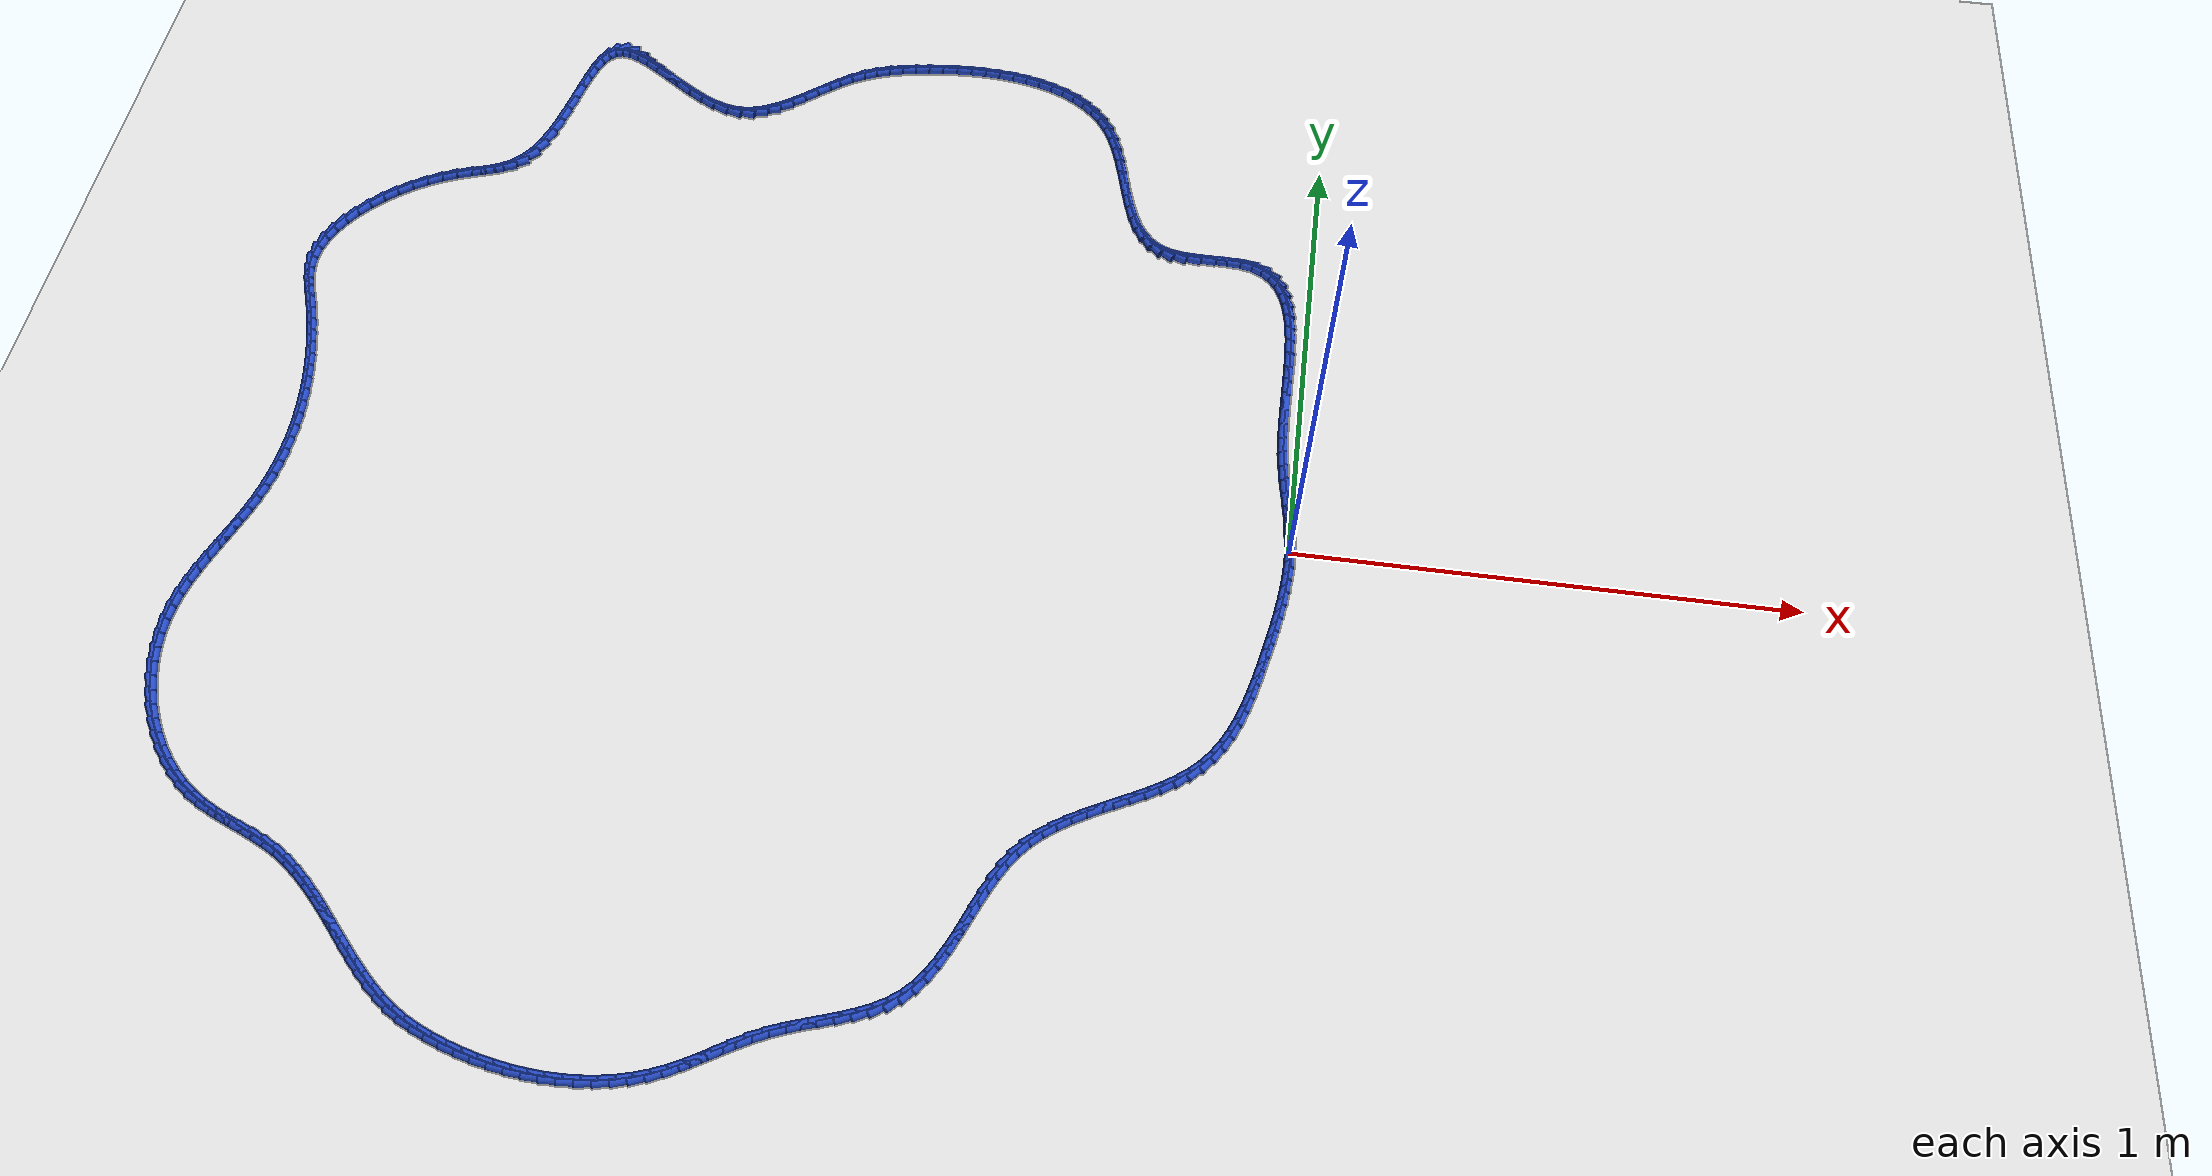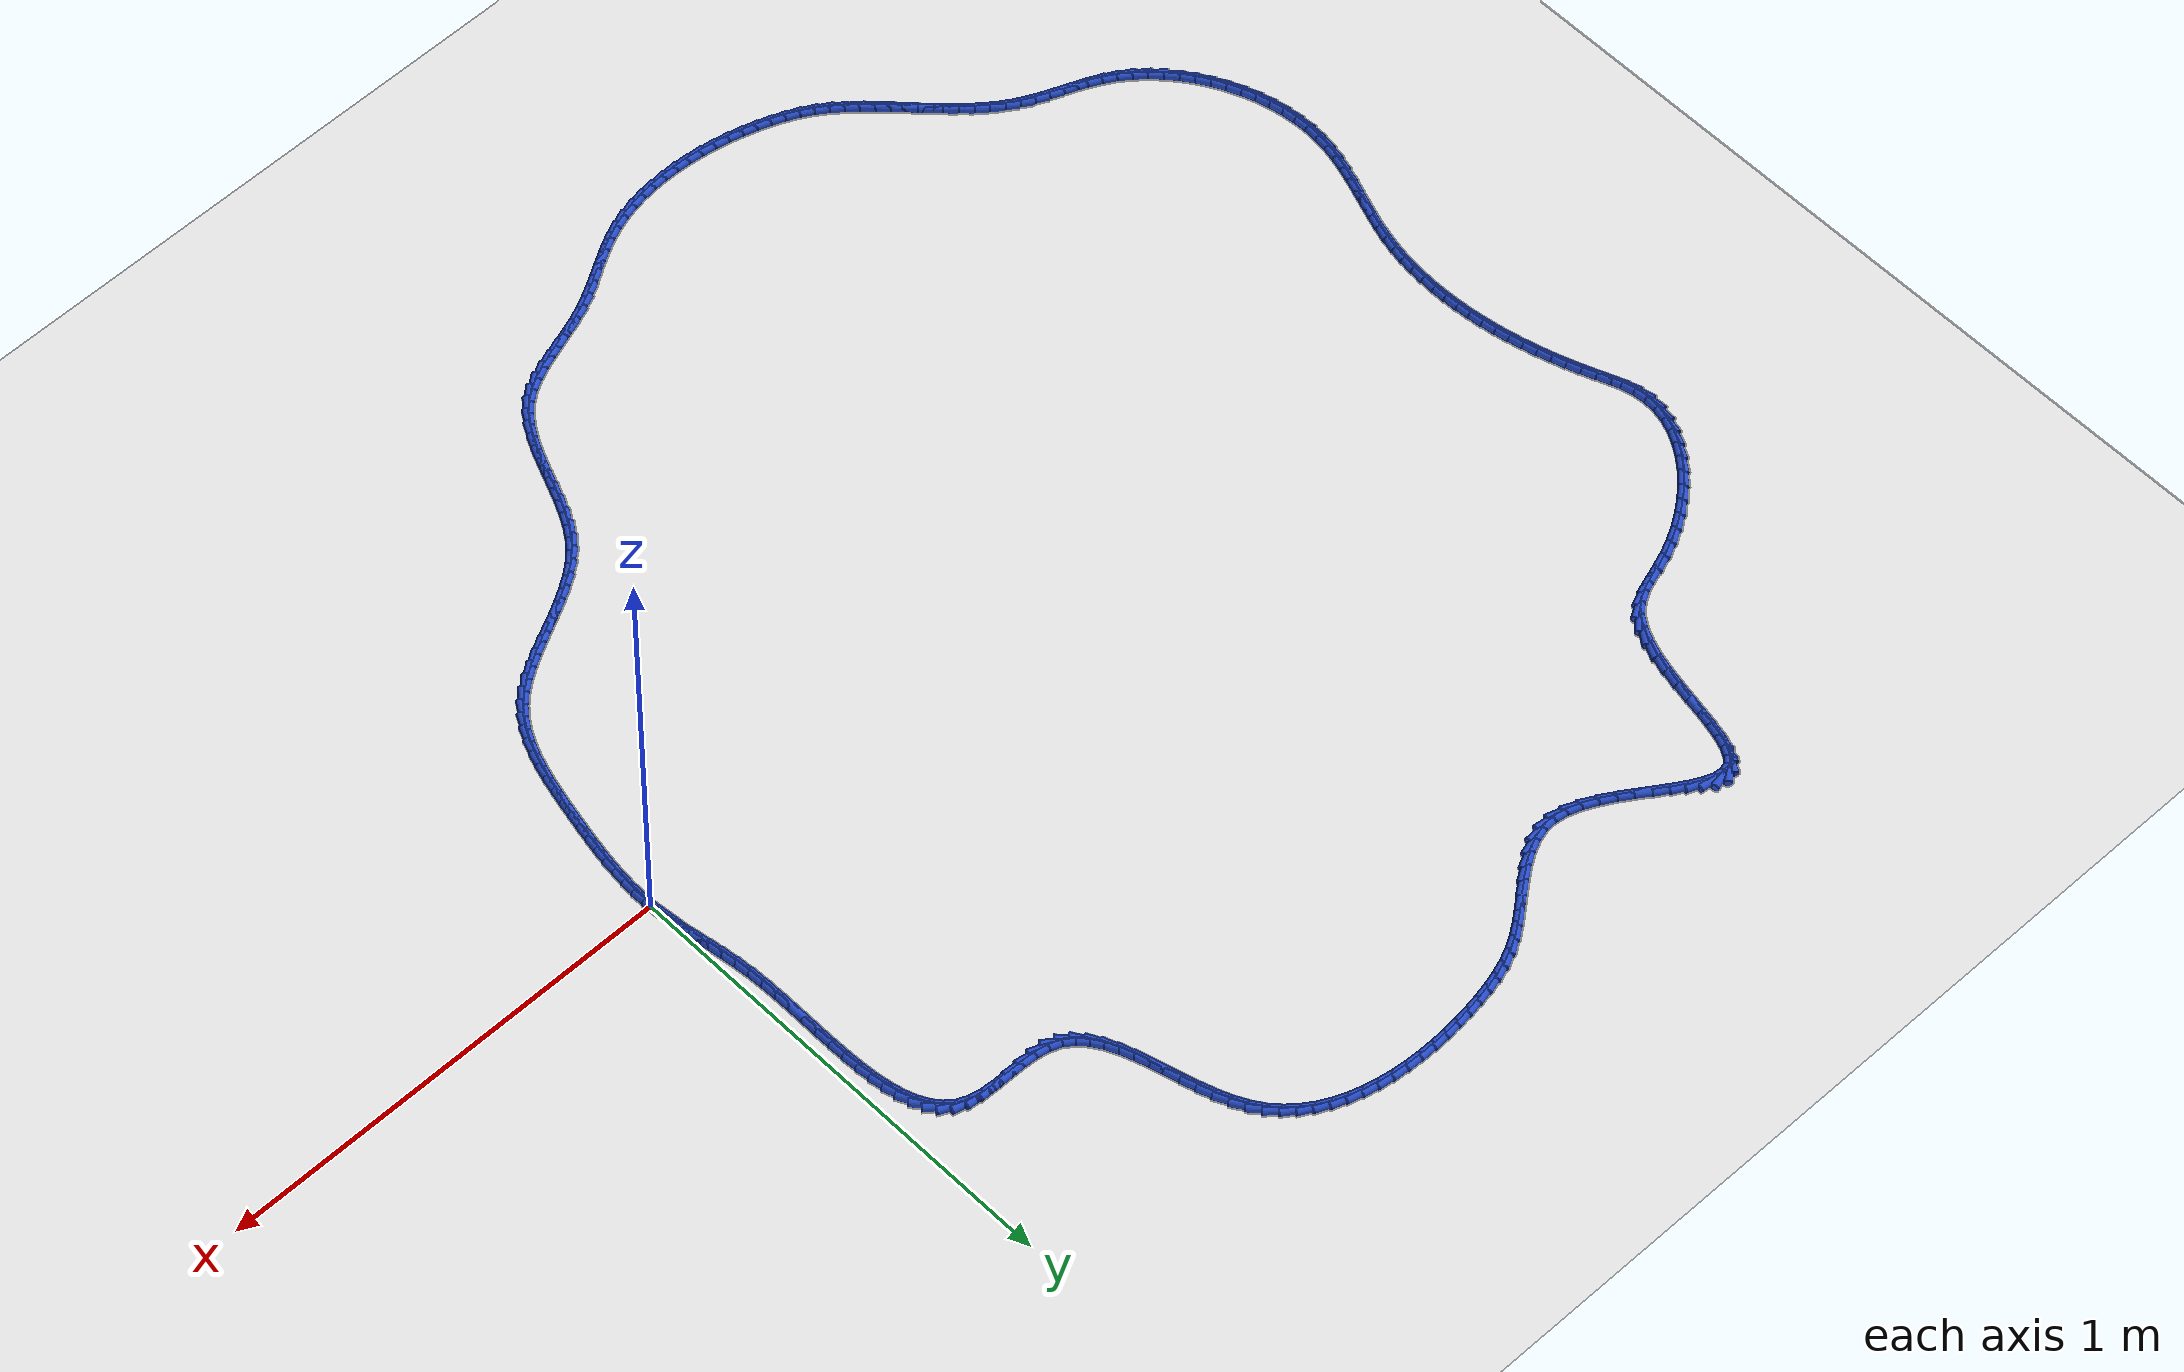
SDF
<sdf version="1.6">
 <world name="default">
  <light name="sun" type="directional">
   <pose>0 0 10 0 -0 0</pose>
   <diffuse>0.8 0.8 0.8 1</diffuse>
   <specular>0.2 0.2 0.2 1</specular>
   <attenuation>
    <range>1000</range>
    <constant>0.9</constant>
    <linear>0.01</linear>
    <quadratic>0.001</quadratic>
   </attenuation>
   <direction>-0.5 0.1 -0.9</direction>
  </light>
  <model name="ground_plane">
   <static>1</static>
   <link name="link">
    <collision name="collision">
     <geometry><plane><normal>0 0 1</normal><size>100 100</size></plane></geometry>
     <surface><friction><ode><mu>100</mu><mu2>50</mu2></ode></friction></surface>
    </collision>
    <visual name="visual">
     <cast_shadows>0</cast_shadows>
     <geometry><plane><normal>0 0 1</normal><size>100 100</size></plane></geometry>
     <material>
      <script><uri>file://media/materials/scripts/gazebo.material</uri><name>Gazebo/WhiteGlow</name></script>
     </material>
    </visual>
   </link>
  </model>
  <gravity>0 0 -9.8</gravity>
  <magnetic_field>6e-06 2.3e-05 -4.2e-05</magnetic_field>
  <atmosphere type="adiabatic"/>
  <physics name="default_physics" default="0" type="ode">
   <max_step_size>0.001</max_step_size>
   <real_time_factor>1</real_time_factor>
   <real_time_update_rate>1000</real_time_update_rate>
  </physics>
  <scene><ambient>0.4 0.4 0.4 1</ambient><background>0.7 0.7 0.7 1</background><shadows>1</shadows></scene>
  <spherical_coordinates>
   <surface_model>EARTH_WGS84</surface_model>
   <latitude_deg>0</latitude_deg>
   <longitude_deg>0</longitude_deg>
   <elevation>0</elevation>
   <heading_deg>0</heading_deg>
  </spherical_coordinates>
  <model name="line">
   <link name="link_0">
    <pose>-6.938893903907228e-18 -1.1102230246251565e-16 0.01 0 1.57 -1.5054571774756562</pose>
    <collision name="collision">
     <geometry><cylinder><radius>0.01</radius><length>0.08</length></cylinder></geometry>
    </collision>
    <visual name="visual">
     <material>
      <script><name>Gazebo/Blue</name><uri>file://media/materials/scripts/gazebo.material</uri></script>
     </material>
     <geometry><cylinder><radius>0.01</radius><length>0.08</length></cylinder></geometry>
    </visual>
   </link>
   <link name="link_1">
    <pose>-0.0018507561572401888 0.028285058413800475 0.01 0 1.57 -1.4603279902830988</pose>
    <collision name="collision">
     <geometry><cylinder><radius>0.01</radius><length>0.08</length></cylinder></geometry>
    </collision>
    <visual name="visual">
     <material>
      <script><name>Gazebo/Blue</name><uri>file://media/materials/scripts/gazebo.material</uri></script>
     </material>
     <geometry><cylinder><radius>0.01</radius><length>0.08</length></cylinder></geometry>
    </visual>
   </link>
   <link name="link_2">
    <pose>-0.004973957591644684 0.05644232753523722 0.01 0 1.57 -1.428864404420115</pose>
    <collision name="collision">
     <geometry><cylinder><radius>0.01</radius><length>0.08</length></cylinder></geometry>
    </collision>
    <visual name="visual">
     <material>
      <script><name>Gazebo/Blue</name><uri>file://media/materials/scripts/gazebo.material</uri></script>
     </material>
     <geometry><cylinder><radius>0.01</radius><length>0.08</length></cylinder></geometry>
    </visual>
   </link>
   <link name="link_3">
    <pose>-0.009013245252917803 0.08471030083472876 0.01 0 1.57 -1.4114505909345159</pose>
    <collision name="collision">
     <geometry><cylinder><radius>0.01</radius><length>0.08</length></cylinder></geometry>
    </collision>
    <visual name="visual">
     <material>
      <script><name>Gazebo/Blue</name><uri>file://media/materials/scripts/gazebo.material</uri></script>
     </material>
     <geometry><cylinder><radius>0.01</radius><length>0.08</length></cylinder></geometry>
    </visual>
   </link>
   <link name="link_4">
    <pose>-0.013612260090763882 0.1133274717826937 0.01 0 1.57 -1.407817067228215</pose>
    <collision name="collision">
     <geometry><cylinder><radius>0.01</radius><length>0.08</length></cylinder></geometry>
    </collision>
    <visual name="visual">
     <material>
      <script><name>Gazebo/Blue</name><uri>file://media/materials/scripts/gazebo.material</uri></script>
     </material>
     <geometry><cylinder><radius>0.01</radius><length>0.08</length></cylinder></geometry>
    </visual>
   </link>
   <link name="link_5">
    <pose>-0.018414643054887242 0.14253233384955064 0.01 0 1.57 -1.4171962833089378</pose>
    <collision name="collision">
     <geometry><cylinder><radius>0.01</radius><length>0.08</length></cylinder></geometry>
    </collision>
    <visual name="visual">
     <material>
      <script><name>Gazebo/Blue</name><uri>file://media/materials/scripts/gazebo.material</uri></script>
     </material>
     <geometry><cylinder><radius>0.01</radius><length>0.08</length></cylinder></geometry>
    </visual>
   </link>
   <link name="link_6">
    <pose>-0.02306403509499219 0.1725633805057181 0.01 0 1.57 -1.4384361056241508</pose>
    <collision name="collision">
     <geometry><cylinder><radius>0.01</radius><length>0.08</length></cylinder></geometry>
    </collision>
    <visual name="visual">
     <material>
      <script><name>Gazebo/Blue</name><uri>file://media/materials/scripts/gazebo.material</uri></script>
     </material>
     <geometry><cylinder><radius>0.01</radius><length>0.08</length></cylinder></geometry>
    </visual>
   </link>
   <link name="link_7">
    <pose>-0.02720407716078306 0.20365910522161473 0.01 0 1.57 -1.4700752066322118</pose>
    <collision name="collision">
     <geometry><cylinder><radius>0.01</radius><length>0.08</length></cylinder></geometry>
    </collision>
    <visual name="visual">
     <material>
      <script><name>Gazebo/Blue</name><uri>file://media/materials/scripts/gazebo.material</uri></script>
     </material>
     <geometry><cylinder><radius>0.01</radius><length>0.08</length></cylinder></geometry>
    </visual>
   </link>
   <link name="link_8">
    <pose>-0.030478410201964172 0.23605800146765918 0.01 0 1.57 -1.5095136919218846</pose>
    <collision name="collision">
     <geometry><cylinder><radius>0.01</radius><length>0.08</length></cylinder></geometry>
    </collision>
    <visual name="visual">
     <material>
      <script><name>Gazebo/Blue</name><uri>file://media/materials/scripts/gazebo.material</uri></script>
     </material>
     <geometry><cylinder><radius>0.01</radius><length>0.08</length></cylinder></geometry>
    </visual>
   </link>
   <link name="link_9">
    <pose>-0.032559363422242346 0.26997213591978664 0.01 0 1.57 -1.543769036115609</pose>
    <collision name="collision">
     <geometry><cylinder><radius>0.01</radius><length>0.08</length></cylinder></geometry>
    </collision>
    <visual name="visual">
     <material>
      <script><name>Gazebo/Blue</name><uri>file://media/materials/scripts/gazebo.material</uri></script>
     </material>
     <geometry><cylinder><radius>0.01</radius><length>0.08</length></cylinder></geometry>
    </visual>
   </link>
   <link name="link_10">
    <pose>-0.033513082443162624 0.30525080289638395 0.01 0 1.57 -1.565865856643343</pose>
    <collision name="collision">
     <geometry><cylinder><radius>0.01</radius><length>0.08</length></cylinder></geometry>
    </collision>
    <visual name="visual">
     <material>
      <script><name>Gazebo/Blue</name><uri>file://media/materials/scripts/gazebo.material</uri></script>
     </material>
     <geometry><cylinder><radius>0.01</radius><length>0.08</length></cylinder></geometry>
    </visual>
   </link>
   <link name="link_11">
    <pose>-0.03369171009792617 0.3414798443100342 0.01 0 1.57 1.564324846531904</pose>
    <collision name="collision">
     <geometry><cylinder><radius>0.01</radius><length>0.08</length></cylinder></geometry>
    </collision>
    <visual name="visual">
     <material>
      <script><name>Gazebo/Blue</name><uri>file://media/materials/scripts/gazebo.material</uri></script>
     </material>
     <geometry><cylinder><radius>0.01</radius><length>0.08</length></cylinder></geometry>
    </visual>
   </link>
   <link name="link_12">
    <pose>-0.03345381946989738 0.37823917871181073 0.01 0 1.57 1.5627726456972344</pose>
    <collision name="collision">
     <geometry><cylinder><radius>0.01</radius><length>0.08</length></cylinder></geometry>
    </collision>
    <visual name="visual">
     <material>
      <script><name>Gazebo/Blue</name><uri>file://media/materials/scripts/gazebo.material</uri></script>
     </material>
     <geometry><cylinder><radius>0.01</radius><length>0.08</length></cylinder></geometry>
    </visual>
   </link>
   <link name="link_13">
    <pose>-0.03315798364244069 0.41510872465278653 0.01 0 1.57 -1.570665251879237</pose>
    <collision name="collision">
     <geometry><cylinder><radius>0.01</radius><length>0.08</length></cylinder></geometry>
    </collision>
    <visual name="visual">
     <material>
      <script><name>Gazebo/Blue</name><uri>file://media/materials/scripts/gazebo.material</uri></script>
     </material>
     <geometry><cylinder><radius>0.01</radius><length>0.08</length></cylinder></geometry>
    </visual>
   </link>
   <link name="link_14">
    <pose>-0.033162775698920476 0.4516684006840346 0.01 0 1.57 -1.5522665436756358</pose>
    <collision name="collision">
     <geometry><cylinder><radius>0.01</radius><length>0.08</length></cylinder></geometry>
    </collision>
    <visual name="visual">
     <material>
      <script><name>Gazebo/Blue</name><uri>file://media/materials/scripts/gazebo.material</uri></script>
     </material>
     <geometry><cylinder><radius>0.01</radius><length>0.08</length></cylinder></geometry>
    </visual>
   </link>
   <link name="link_15">
    <pose>-0.03382676872270118 0.48749812535662834 0.01 0 1.57 -1.5223399967057758</pose>
    <collision name="collision">
     <geometry><cylinder><radius>0.01</radius><length>0.08</length></cylinder></geometry>
    </collision>
    <visual name="visual">
     <material>
      <script><name>Gazebo/Blue</name><uri>file://media/materials/scripts/gazebo.material</uri></script>
     </material>
     <geometry><cylinder><radius>0.01</radius><length>0.08</length></cylinder></geometry>
    </visual>
   </link>
   <link name="link_16">
    <pose>-0.03550853579714719 0.5221778172216409 0.01 0 1.57 -1.4786942097951852</pose>
    <collision name="collision">
     <geometry><cylinder><radius>0.01</radius><length>0.08</length></cylinder></geometry>
    </collision>
    <visual name="visual">
     <material>
      <script><name>Gazebo/Blue</name><uri>file://media/materials/scripts/gazebo.material</uri></script>
     </material>
     <geometry><cylinder><radius>0.01</radius><length>0.08</length></cylinder></geometry>
    </visual>
   </link>
   <link name="link_17">
    <pose>-0.03856665000562291 0.5552873948301452 0.01 0 1.57 -1.4179763216596335</pose>
    <collision name="collision">
     <geometry><cylinder><radius>0.01</radius><length>0.08</length></cylinder></geometry>
    </collision>
    <visual name="visual">
     <material>
      <script><name>Gazebo/Blue</name><uri>file://media/materials/scripts/gazebo.material</uri></script>
     </material>
     <geometry><cylinder><radius>0.01</radius><length>0.08</length></cylinder></geometry>
    </visual>
   </link>
   <link name="link_18">
    <pose>-0.04335968443149279 0.586406776733215 0.01 0 1.57 -1.3353718067991045</pose>
    <collision name="collision">
     <geometry><cylinder><radius>0.01</radius><length>0.08</length></cylinder></geometry>
    </collision>
    <visual name="visual">
     <material>
      <script><name>Gazebo/Blue</name><uri>file://media/materials/scripts/gazebo.material</uri></script>
     </material>
     <geometry><cylinder><radius>0.01</radius><length>0.08</length></cylinder></geometry>
    </visual>
   </link>
   <link name="link_19">
    <pose>-0.05024621215812118 0.6151158814819225 0.01 0 1.57 -1.2244799730533134</pose>
    <collision name="collision">
     <geometry><cylinder><radius>0.01</radius><length>0.08</length></cylinder></geometry>
    </collision>
    <visual name="visual">
     <material>
      <script><name>Gazebo/Blue</name><uri>file://media/materials/scripts/gazebo.material</uri></script>
     </material>
     <geometry><cylinder><radius>0.01</radius><length>0.08</length></cylinder></geometry>
    </visual>
   </link>
   <link name="link_20">
    <pose>-0.05958480626887254 0.6409946276273418 0.01 0 1.57 -1.0780630029013674</pose>
    <collision name="collision">
     <geometry><cylinder><radius>0.01</radius><length>0.08</length></cylinder></geometry>
    </collision>
    <visual name="visual">
     <material>
      <script><name>Gazebo/Blue</name><uri>file://media/materials/scripts/gazebo.material</uri></script>
     </material>
     <geometry><cylinder><radius>0.01</radius><length>0.08</length></cylinder></geometry>
    </visual>
   </link>
   <link name="link_21">
    <pose>-0.07173403984711127 0.6636229337205454 0.01 0 1.57 -0.8911785869316133</pose>
    <collision name="collision">
     <geometry><cylinder><radius>0.01</radius><length>0.08</length></cylinder></geometry>
    </collision>
    <visual name="visual">
     <material>
      <script><name>Gazebo/Blue</name><uri>file://media/materials/scripts/gazebo.material</uri></script>
     </material>
     <geometry><cylinder><radius>0.01</radius><length>0.08</length></cylinder></geometry>
    </visual>
   </link>
   <link name="link_22">
    <pose>-0.08705248597620173 0.6825807183126067 0.01 0 1.57 -0.6679159367749155</pose>
    <collision name="collision">
     <geometry><cylinder><radius>0.01</radius><length>0.08</length></cylinder></geometry>
    </collision>
    <visual name="visual">
     <material>
      <script><name>Gazebo/Blue</name><uri>file://media/materials/scripts/gazebo.material</uri></script>
     </material>
     <geometry><cylinder><radius>0.01</radius><length>0.08</length></cylinder></geometry>
    </visual>
   </link>
   <link name="link_23">
    <pose>-0.1058987177395084 0.697447899954599 0.01 0 1.57 -0.42748396133746797</pose>
    <collision name="collision">
     <geometry><cylinder><radius>0.01</radius><length>0.08</length></cylinder></geometry>
    </collision>
    <visual name="visual">
     <material>
      <script><name>Gazebo/Blue</name><uri>file://media/materials/scripts/gazebo.material</uri></script>
     </material>
     <geometry><cylinder><radius>0.01</radius><length>0.08</length></cylinder></geometry>
    </visual>
   </link>
   <link name="link_24">
    <pose>-0.12863130822039573 0.7078043971975954 0.01 0 1.57 -0.20870144032498317</pose>
    <collision name="collision">
     <geometry><cylinder><radius>0.01</radius><length>0.08</length></cylinder></geometry>
    </collision>
    <visual name="visual">
     <material>
      <script><name>Gazebo/Blue</name><uri>file://media/materials/scripts/gazebo.material</uri></script>
     </material>
     <geometry><cylinder><radius>0.01</radius><length>0.08</length></cylinder></geometry>
    </visual>
   </link>
   <link name="link_25">
    <pose>-0.15540791957663663 0.7134752889670596 0.01 0 1.57 -0.07275181994475947</pose>
    <collision name="collision">
     <geometry><cylinder><radius>0.01</radius><length>0.08</length></cylinder></geometry>
    </collision>
    <visual name="visual">
     <material>
      <script><name>Gazebo/Blue</name><uri>file://media/materials/scripts/gazebo.material</uri></script>
     </material>
     <geometry><cylinder><radius>0.01</radius><length>0.08</length></cylinder></geometry>
    </visual>
   </link>
   <link name="link_26">
    <pose>-0.18526695078669697 0.7156514284950204 0.01 0 1.57 -0.010921333018388352</pose>
    <collision name="collision">
     <geometry><cylinder><radius>0.01</radius><length>0.08</length></cylinder></geometry>
    </collision>
    <visual name="visual">
     <material>
      <script><name>Gazebo/Blue</name><uri>file://media/materials/scripts/gazebo.material</uri></script>
     </material>
     <geometry><cylinder><radius>0.01</radius><length>0.08</length></cylinder></geometry>
    </visual>
   </link>
   <link name="link_27">
    <pose>-0.21685933398335697 0.7159964731513244 0.01 0 1.57 -0.005568607727887532</pose>
    <collision name="collision">
     <geometry><cylinder><radius>0.01</radius><length>0.08</length></cylinder></geometry>
    </collision>
    <visual name="visual">
     <material>
      <script><name>Gazebo/Blue</name><uri>file://media/materials/scripts/gazebo.material</uri></script>
     </material>
     <geometry><cylinder><radius>0.01</radius><length>0.08</length></cylinder></geometry>
    </visual>
   </link>
   <link name="link_28">
    <pose>-0.2488356258727135 0.7161745384180177 0.01 0 1.57 -0.05396755352213023</pose>
    <collision name="collision">
     <geometry><cylinder><radius>0.01</radius><length>0.08</length></cylinder></geometry>
    </collision>
    <visual name="visual">
     <material>
      <script><name>Gazebo/Blue</name><uri>file://media/materials/scripts/gazebo.material</uri></script>
     </material>
     <geometry><cylinder><radius>0.01</radius><length>0.08</length></cylinder></geometry>
    </visual>
   </link>
   <link name="link_29">
    <pose>-0.27984638316086347 0.7178497397771471 0.01 0 1.57 -0.16697307033068925</pose>
    <collision name="collision">
     <geometry><cylinder><radius>0.01</radius><length>0.08</length></cylinder></geometry>
    </collision>
    <visual name="visual">
     <material>
      <script><name>Gazebo/Blue</name><uri>file://media/materials/scripts/gazebo.material</uri></script>
     </material>
     <geometry><cylinder><radius>0.01</radius><length>0.08</length></cylinder></geometry>
    </visual>
   </link>
   <link name="link_30">
    <pose>-0.30854216255390365 0.7226861927107595 0.01 0 1.57 -0.36575165464676584</pose>
    <collision name="collision">
     <geometry><cylinder><radius>0.01</radius><length>0.08</length></cylinder></geometry>
    </collision>
    <visual name="visual">
     <material>
      <script><name>Gazebo/Blue</name><uri>file://media/materials/scripts/gazebo.material</uri></script>
     </material>
     <geometry><cylinder><radius>0.01</radius><length>0.08</length></cylinder></geometry>
    </visual>
   </link>
   <link name="link_31">
    <pose>-0.3336204085279111 0.7322907525275851 0.01 0 1.57 -0.612045686818249</pose>
    <collision name="collision">
     <geometry><cylinder><radius>0.01</radius><length>0.08</length></cylinder></geometry>
    </collision>
    <visual name="visual">
     <material>
      <script><name>Gazebo/Blue</name><uri>file://media/materials/scripts/gazebo.material</uri></script>
     </material>
     <geometry><cylinder><radius>0.01</radius><length>0.08</length></cylinder></geometry>
    </visual>
   </link>
   <link name="link_32">
    <pose>-0.35472966274941314 0.7471087778392641 0.01 0 1.57 -0.831805815628706</pose>
    <collision name="collision">
     <geometry><cylinder><radius>0.01</radius><length>0.08</length></cylinder></geometry>
    </collision>
    <visual name="visual">
     <material>
      <script><name>Gazebo/Blue</name><uri>file://media/materials/scripts/gazebo.material</uri></script>
     </material>
     <geometry><cylinder><radius>0.01</radius><length>0.08</length></cylinder></geometry>
    </visual>
   </link>
   <link name="link_33">
    <pose>-0.37240378605322877 0.7665044598434593 0.01 0 1.57 -1.0046292670729737</pose>
    <collision name="collision">
     <geometry><cylinder><radius>0.01</radius><length>0.08</length></cylinder></geometry>
    </collision>
    <visual name="visual">
     <material>
      <script><name>Gazebo/Blue</name><uri>file://media/materials/scripts/gazebo.material</uri></script>
     </material>
     <geometry><cylinder><radius>0.01</radius><length>0.08</length></cylinder></geometry>
    </visual>
   </link>
   <link name="link_34">
    <pose>-0.38721035025383926 0.789800821293717 0.01 0 1.57 -1.130134532932898</pose>
    <collision name="collision">
     <geometry><cylinder><radius>0.01</radius><length>0.08</length></cylinder></geometry>
    </collision>
    <visual name="visual">
     <material>
      <script><name>Gazebo/Blue</name><uri>file://media/materials/scripts/gazebo.material</uri></script>
     </material>
     <geometry><cylinder><radius>0.01</radius><length>0.08</length></cylinder></geometry>
    </visual>
   </link>
   <link name="link_35">
    <pose>-0.39971692716572577 0.8163208849435838 0.01 0 1.57 -1.2158279734016342</pose>
    <collision name="collision">
     <geometry><cylinder><radius>0.01</radius><length>0.08</length></cylinder></geometry>
    </collision>
    <visual name="visual">
     <material>
      <script><name>Gazebo/Blue</name><uri>file://media/materials/scripts/gazebo.material</uri></script>
     </material>
     <geometry><cylinder><radius>0.01</radius><length>0.08</length></cylinder></geometry>
    </visual>
   </link>
   <link name="link_36">
    <pose>-0.41049108860336964 0.8453876735466065 0.01 0 1.57 -1.2696306897173477</pose>
    <collision name="collision">
     <geometry><cylinder><radius>0.01</radius><length>0.08</length></cylinder></geometry>
    </collision>
    <visual name="visual">
     <material>
      <script><name>Gazebo/Blue</name><uri>file://media/materials/scripts/gazebo.material</uri></script>
     </material>
     <geometry><cylinder><radius>0.01</radius><length>0.08</length></cylinder></geometry>
    </visual>
   </link>
   <link name="link_37">
    <pose>-0.4201004063812523 0.8763242098563314 0.01 0 1.57 -1.2973305151649175</pose>
    <collision name="collision">
     <geometry><cylinder><radius>0.01</radius><length>0.08</length></cylinder></geometry>
    </collision>
    <visual name="visual">
     <material>
      <script><name>Gazebo/Blue</name><uri>file://media/materials/scripts/gazebo.material</uri></script>
     </material>
     <geometry><cylinder><radius>0.01</radius><length>0.08</length></cylinder></geometry>
    </visual>
   </link>
   <link name="link_38">
    <pose>-0.4291124523138549 0.9084535166263059 0.01 0 1.57 -1.3022893392485444</pose>
    <collision name="collision">
     <geometry><cylinder><radius>0.01</radius><length>0.08</length></cylinder></geometry>
    </collision>
    <visual name="visual">
     <material>
      <script><name>Gazebo/Blue</name><uri>file://media/materials/scripts/gazebo.material</uri></script>
     </material>
     <geometry><cylinder><radius>0.01</radius><length>0.08</length></cylinder></geometry>
    </visual>
   </link>
   <link name="link_39">
    <pose>-0.43809479821565883 0.9410986166100758 0.01 0 1.57 -1.285704959052395</pose>
    <collision name="collision">
     <geometry><cylinder><radius>0.01</radius><length>0.08</length></cylinder></geometry>
    </collision>
    <visual name="visual">
     <material>
      <script><name>Gazebo/Blue</name><uri>file://media/materials/scripts/gazebo.material</uri></script>
     </material>
     <geometry><cylinder><radius>0.01</radius><length>0.08</length></cylinder></geometry>
    </visual>
   </link>
   <link name="link_40">
    <pose>-0.44761501590114544 0.9735825325611884 0.01 0 1.57 -1.2468553366133452</pose>
    <collision name="collision">
     <geometry><cylinder><radius>0.01</radius><length>0.08</length></cylinder></geometry>
    </collision>
    <visual name="visual">
     <material>
      <script><name>Gazebo/Blue</name><uri>file://media/materials/scripts/gazebo.material</uri></script>
     </material>
     <geometry><cylinder><radius>0.01</radius><length>0.08</length></cylinder></geometry>
    </visual>
   </link>
   <link name="link_41">
    <pose>-0.4582406771847959 1.0052282872331904 0.01 0 1.57 -1.1832592630384855</pose>
    <collision name="collision">
     <geometry><cylinder><radius>0.01</radius><length>0.08</length></cylinder></geometry>
    </collision>
    <visual name="visual">
     <material>
      <script><name>Gazebo/Blue</name><uri>file://media/materials/scripts/gazebo.material</uri></script>
     </material>
     <geometry><cylinder><radius>0.01</radius><length>0.08</length></cylinder></geometry>
    </visual>
   </link>
   <link name="link_42">
    <pose>-0.47053935388109147 1.0353589033796275 0.01 0 1.57 -1.0909603004029662</pose>
    <collision name="collision">
     <geometry><cylinder><radius>0.01</radius><length>0.08</length></cylinder></geometry>
    </collision>
    <visual name="visual">
     <material>
      <script><name>Gazebo/Blue</name><uri>file://media/materials/scripts/gazebo.material</uri></script>
     </material>
     <geometry><cylinder><radius>0.01</radius><length>0.08</length></cylinder></geometry>
    </visual>
   </link>
   <link name="link_43">
    <pose>-0.4850786178045136 1.0632974037540477 0.01 0 1.57 -0.9682531319410803</pose>
    <collision name="collision">
     <geometry><cylinder><radius>0.01</radius><length>0.08</length></cylinder></geometry>
    </collision>
    <visual name="visual">
     <material>
      <script><name>Gazebo/Blue</name><uri>file://media/materials/scripts/gazebo.material</uri></script>
     </material>
     <geometry><cylinder><radius>0.01</radius><length>0.08</length></cylinder></geometry>
    </visual>
   </link>
   <link name="link_44">
    <pose>-0.5023645933400334 1.0884268665331065 0.01 0 1.57 -0.8368560827267585</pose>
    <collision name="collision">
     <geometry><cylinder><radius>0.01</radius><length>0.08</length></cylinder></geometry>
    </collision>
    <visual name="visual">
     <material>
      <script><name>Gazebo/Blue</name><uri>file://media/materials/scripts/gazebo.material</uri></script>
     </material>
     <geometry><cylinder><radius>0.01</radius><length>0.08</length></cylinder></geometry>
    </visual>
   </link>
   <link name="link_45">
    <pose>-0.5223924502466633 1.1106297495501276 0.01 0 1.57 -0.7114532544425247</pose>
    <collision name="collision">
     <geometry><cylinder><radius>0.01</radius><length>0.08</length></cylinder></geometry>
    </collision>
    <visual name="visual">
     <material>
      <script><name>Gazebo/Blue</name><uri>file://media/materials/scripts/gazebo.material</uri></script>
     </material>
     <geometry><cylinder><radius>0.01</radius><length>0.08</length></cylinder></geometry>
    </visual>
   </link>
   <link name="link_46">
    <pose>-0.544904055386851 1.1300360753087444 0.01 0 1.57 -0.5950031883651092</pose>
    <collision name="collision">
     <geometry><cylinder><radius>0.01</radius><length>0.08</length></cylinder></geometry>
    </collision>
    <visual name="visual">
     <material>
      <script><name>Gazebo/Blue</name><uri>file://media/materials/scripts/gazebo.material</uri></script>
     </material>
     <geometry><cylinder><radius>0.01</radius><length>0.08</length></cylinder></geometry>
    </visual>
   </link>
   <link name="link_47">
    <pose>-0.5696394572779547 1.1467776434655916 0.01 0 1.57 -0.48905327663435233</pose>
    <collision name="collision">
     <geometry><cylinder><radius>0.01</radius><length>0.08</length></cylinder></geometry>
    </collision>
    <visual name="visual">
     <material>
      <script><name>Gazebo/Blue</name><uri>file://media/materials/scripts/gazebo.material</uri></script>
     </material>
     <geometry><cylinder><radius>0.01</radius><length>0.08</length></cylinder></geometry>
    </visual>
   </link>
   <link name="link_48">
    <pose>-0.5963387044373322 1.1609862536773032 0.01 0 1.57 -0.39397516067728205</pose>
    <collision name="collision">
     <geometry><cylinder><radius>0.01</radius><length>0.08</length></cylinder></geometry>
    </collision>
    <visual name="visual">
     <material>
      <script><name>Gazebo/Blue</name><uri>file://media/materials/scripts/gazebo.material</uri></script>
     </material>
     <geometry><cylinder><radius>0.01</radius><length>0.08</length></cylinder></geometry>
    </visual>
   </link>
   <link name="link_49">
    <pose>-0.6247418453823417 1.1727937056005149 0.01 0 1.57 -0.3093086091629866</pose>
    <collision name="collision">
     <geometry><cylinder><radius>0.01</radius><length>0.08</length></cylinder></geometry>
    </collision>
    <visual name="visual">
     <material>
      <script><name>Gazebo/Blue</name><uri>file://media/materials/scripts/gazebo.material</uri></script>
     </material>
     <geometry><cylinder><radius>0.01</radius><length>0.08</length></cylinder></geometry>
    </visual>
   </link>
   <link name="link_50">
    <pose>-0.6545889286303403 1.1823317988918594 0.01 0 1.57 -0.23411470245884441</pose>
    <collision name="collision">
     <geometry><cylinder><radius>0.01</radius><length>0.08</length></cylinder></geometry>
    </collision>
    <visual name="visual">
     <material>
      <script><name>Gazebo/Blue</name><uri>file://media/materials/scripts/gazebo.material</uri></script>
     </material>
     <geometry><cylinder><radius>0.01</radius><length>0.08</length></cylinder></geometry>
    </visual>
   </link>
   <link name="link_51">
    <pose>-0.685620002698687 1.1897323332079721 0.01 0 1.57 -0.1672465088260299</pose>
    <collision name="collision">
     <geometry><cylinder><radius>0.01</radius><length>0.08</length></cylinder></geometry>
    </collision>
    <visual name="visual">
     <material>
      <script><name>Gazebo/Blue</name><uri>file://media/materials/scripts/gazebo.material</uri></script>
     </material>
     <geometry><cylinder><radius>0.01</radius><length>0.08</length></cylinder></geometry>
    </visual>
   </link>
   <link name="link_52">
    <pose>-0.717575116104739 1.1951271082054875 0.01 0 1.57 -0.107520633574932</pose>
    <collision name="collision">
     <geometry><cylinder><radius>0.01</radius><length>0.08</length></cylinder></geometry>
    </collision>
    <visual name="visual">
     <material>
      <script><name>Gazebo/Blue</name><uri>file://media/materials/scripts/gazebo.material</uri></script>
     </material>
     <geometry><cylinder><radius>0.01</radius><length>0.08</length></cylinder></geometry>
    </visual>
   </link>
   <link name="link_53">
    <pose>-0.7501943173658542 1.19864792354104 0.01 0 1.57 -0.05380856416560193</pose>
    <collision name="collision">
     <geometry><cylinder><radius>0.01</radius><length>0.08</length></cylinder></geometry>
    </collision>
    <visual name="visual">
     <material>
      <script><name>Gazebo/Blue</name><uri>file://media/materials/scripts/gazebo.material</uri></script>
     </material>
     <geometry><cylinder><radius>0.01</radius><length>0.08</length></cylinder></geometry>
    </visual>
   </link>
   <link name="link_54">
    <pose>-0.7832176549993908 1.200426578871264 0.01 0 1.57 -0.0050740460673506784</pose>
    <collision name="collision">
     <geometry><cylinder><radius>0.01</radius><length>0.08</length></cylinder></geometry>
    </collision>
    <visual name="visual">
     <material>
      <script><name>Gazebo/Blue</name><uri>file://media/materials/scripts/gazebo.material</uri></script>
     </material>
     <geometry><cylinder><radius>0.01</radius><length>0.08</length></cylinder></geometry>
    </visual>
   </link>
   <link name="link_55">
    <pose>-0.8163851775227068 1.200594873852794 0.01 0 1.57 0.03962209979863795</pose>
    <collision name="collision">
     <geometry><cylinder><radius>0.01</radius><length>0.08</length></cylinder></geometry>
    </collision>
    <visual name="visual">
     <material>
      <script><name>Gazebo/Blue</name><uri>file://media/materials/scripts/gazebo.material</uri></script>
     </material>
     <geometry><cylinder><radius>0.01</radius><length>0.08</length></cylinder></geometry>
    </visual>
   </link>
   <link name="link_56">
    <pose>-0.8494369334531598 1.1992846081422643 0.01 0 1.57 0.08113571758164483</pose>
    <collision name="collision">
     <geometry><cylinder><radius>0.01</radius><length>0.08</length></cylinder></geometry>
    </collision>
    <visual name="visual">
     <material>
      <script><name>Gazebo/Blue</name><uri>file://media/materials/scripts/gazebo.material</uri></script>
     </material>
     <geometry><cylinder><radius>0.01</radius><length>0.08</length></cylinder></geometry>
    </visual>
   </link>
   <link name="link_57">
    <pose>-0.8821129713081082 1.1966275813963099 0.01 0 1.57 0.12026399499485653</pose>
    <collision name="collision">
     <geometry><cylinder><radius>0.01</radius><length>0.08</length></cylinder></geometry>
    </collision>
    <visual name="visual">
     <material>
      <script><name>Gazebo/Blue</name><uri>file://media/materials/scripts/gazebo.material</uri></script>
     </material>
     <geometry><cylinder><radius>0.01</radius><length>0.08</length></cylinder></geometry>
    </visual>
   </link>
   <link name="link_58">
    <pose>-0.9141533396049092 1.192755593271564 0.01 0 1.57 0.15778171728028711</pose>
    <collision name="collision">
     <geometry><cylinder><radius>0.01</radius><length>0.08</length></cylinder></geometry>
    </collision>
    <visual name="visual">
     <material>
      <script><name>Gazebo/Blue</name><uri>file://media/materials/scripts/gazebo.material</uri></script>
     </material>
     <geometry><cylinder><radius>0.01</radius><length>0.08</length></cylinder></geometry>
    </visual>
   </link>
   <link name="link_59">
    <pose>-0.9452981631344576 1.1878003205004048 0.01 0 1.57 0.19815385010009096</pose>
    <collision name="collision">
     <geometry><cylinder><radius>0.01</radius><length>0.08</length></cylinder></geometry>
    </collision>
    <visual name="visual">
     <material>
      <script><name>Gazebo/Blue</name><uri>file://media/materials/scripts/gazebo.material</uri></script>
     </material>
     <geometry><cylinder><radius>0.01</radius><length>0.08</length></cylinder></geometry>
    </visual>
   </link>
   <link name="link_60">
    <pose>-0.9753688333845228 1.1817624684609112 0.01 0 1.57 0.2526118643670511</pose>
    <collision name="collision">
     <geometry><cylinder><radius>0.01</radius><length>0.08</length></cylinder></geometry>
    </collision>
    <visual name="visual">
     <material>
      <script><name>Gazebo/Blue</name><uri>file://media/materials/scripts/gazebo.material</uri></script>
     </material>
     <geometry><cylinder><radius>0.01</radius><length>0.08</length></cylinder></geometry>
    </visual>
   </link>
   <link name="link_61">
    <pose>-1.0044223711567437 1.174262996687704 0.01 0 1.57 0.3227078107218876</pose>
    <collision name="collision">
     <geometry><cylinder><radius>0.01</radius><length>0.08</length></cylinder></geometry>
    </collision>
    <visual name="visual">
     <material>
      <script><name>Gazebo/Blue</name><uri>file://media/materials/scripts/gazebo.material</uri></script>
     </material>
     <geometry><cylinder><radius>0.01</radius><length>0.08</length></cylinder></geometry>
    </visual>
   </link>
   <link name="link_62">
    <pose>-1.0325582592678613 1.1648544319152805 0.01 0 1.57 0.40666979276354287</pose>
    <collision name="collision">
     <geometry><cylinder><radius>0.01</radius><length>0.08</length></cylinder></geometry>
    </collision>
    <visual name="visual">
     <material>
      <script><name>Gazebo/Blue</name><uri>file://media/materials/scripts/gazebo.material</uri></script>
     </material>
     <geometry><cylinder><radius>0.01</radius><length>0.08</length></cylinder></geometry>
    </visual>
   </link>
   <link name="link_63">
    <pose>-1.059875980534617 1.153089300878136 0.01 0 1.57 0.5009448567318048</pose>
    <collision name="collision">
     <geometry><cylinder><radius>0.01</radius><length>0.08</length></cylinder></geometry>
    </collision>
    <visual name="visual">
     <material>
      <script><name>Gazebo/Blue</name><uri>file://media/materials/scripts/gazebo.material</uri></script>
     </material>
     <geometry><cylinder><radius>0.01</radius><length>0.08</length></cylinder></geometry>
    </visual>
   </link>
   <link name="link_64">
    <pose>-1.086475341348815 1.1385253536591375 0.01 0 1.57 0.587125376779683</pose>
    <collision name="collision">
     <geometry><cylinder><radius>0.01</radius><length>0.08</length></cylinder></geometry>
    </collision>
    <visual name="visual">
     <material>
      <script><name>Gazebo/Blue</name><uri>file://media/materials/scripts/gazebo.material</uri></script>
     </material>
     <geometry><cylinder><radius>0.01</radius><length>0.08</length></cylinder></geometry>
    </visual>
   </link>
   <link name="link_65">
    <pose>-1.1124869296426356 1.1212172349632477 0.01 0 1.57 0.6407535852951146</pose>
    <collision name="collision">
     <geometry><cylinder><radius>0.01</radius><length>0.08</length></cylinder></geometry>
    </collision>
    <visual name="visual">
     <material>
      <script><name>Gazebo/Blue</name><uri>file://media/materials/scripts/gazebo.material</uri></script>
     </material>
     <geometry><cylinder><radius>0.01</radius><length>0.08</length></cylinder></geometry>
    </visual>
   </link>
   <link name="link_66">
    <pose>-1.138097071387128 1.1021193473184996 0.01 0 1.57 0.6630561135025415</pose>
    <collision name="collision">
     <geometry><cylinder><radius>0.01</radius><length>0.08</length></cylinder></geometry>
    </collision>
    <visual name="visual">
     <material>
      <script><name>Gazebo/Blue</name><uri>file://media/materials/scripts/gazebo.material</uri></script>
     </material>
     <geometry><cylinder><radius>0.01</radius><length>0.08</length></cylinder></geometry>
    </visual>
   </link>
   <link name="link_67">
    <pose>-1.1634979659799358 1.0822809057299072 0.01 0 1.57 0.6557882963308712</pose>
    <collision name="collision">
     <geometry><cylinder><radius>0.01</radius><length>0.08</length></cylinder></geometry>
    </collision>
    <visual name="visual">
     <material>
      <script><name>Gazebo/Blue</name><uri>file://media/materials/scripts/gazebo.material</uri></script>
     </material>
     <geometry><cylinder><radius>0.01</radius><length>0.08</length></cylinder></geometry>
    </visual>
   </link>
   <link name="link_68">
    <pose>-1.1888818128187038 1.0627511252024853 0.01 0 1.57 0.618056303916666</pose>
    <collision name="collision">
     <geometry><cylinder><radius>0.01</radius><length>0.08</length></cylinder></geometry>
    </collision>
    <visual name="visual">
     <material>
      <script><name>Gazebo/Blue</name><uri>file://media/materials/scripts/gazebo.material</uri></script>
     </material>
     <geometry><cylinder><radius>0.01</radius><length>0.08</length></cylinder></geometry>
    </visual>
   </link>
   <link name="link_69">
    <pose>-1.2144408113010754 1.044579220741249 0.01 0 1.57 0.5463259533520801</pose>
    <collision name="collision">
     <geometry><cylinder><radius>0.01</radius><length>0.08</length></cylinder></geometry>
    </collision>
    <visual name="visual">
     <material>
      <script><name>Gazebo/Blue</name><uri>file://media/materials/scripts/gazebo.material</uri></script>
     </material>
     <geometry><cylinder><radius>0.01</radius><length>0.08</length></cylinder></geometry>
    </visual>
   </link>
   <link name="link_70">
    <pose>-1.240367160824695 1.0288144073512127 0.01 0 1.57 0.4350268030249729</pose>
    <collision name="collision">
     <geometry><cylinder><radius>0.01</radius><length>0.08</length></cylinder></geometry>
    </collision>
    <visual name="visual">
     <material>
      <script><name>Gazebo/Blue</name><uri>file://media/materials/scripts/gazebo.material</uri></script>
     </material>
     <geometry><cylinder><radius>0.01</radius><length>0.08</length></cylinder></geometry>
    </visual>
   </link>
   <link name="link_71">
    <pose>-1.2668530607872064 1.0165059000373915 0.01 0 1.57 0.2790055510104532</pose>
    <collision name="collision">
     <geometry><cylinder><radius>0.01</radius><length>0.08</length></cylinder></geometry>
    </collision>
    <visual name="visual">
     <material>
      <script><name>Gazebo/Blue</name><uri>file://media/materials/scripts/gazebo.material</uri></script>
     </material>
     <geometry><cylinder><radius>0.01</radius><length>0.08</length></cylinder></geometry>
    </visual>
   </link>
   <link name="link_72">
    <pose>-1.294090710586254 1.0087029138048 0.01 0 1.57 0.07960863686700781</pose>
    <collision name="collision">
     <geometry><cylinder><radius>0.01</radius><length>0.08</length></cylinder></geometry>
    </collision>
    <visual name="visual">
     <material>
      <script><name>Gazebo/Blue</name><uri>file://media/materials/scripts/gazebo.material</uri></script>
     </material>
     <geometry><cylinder><radius>0.01</radius><length>0.08</length></cylinder></geometry>
    </visual>
   </link>
   <link name="link_73">
    <pose>-1.3222723096194808 1.006454663658453 0.01 0 1.57 -0.14136464432406018</pose>
    <collision name="collision">
     <geometry><cylinder><radius>0.01</radius><length>0.08</length></cylinder></geometry>
    </collision>
    <visual name="visual">
     <material>
      <script><name>Gazebo/Blue</name><uri>file://media/materials/scripts/gazebo.material</uri></script>
     </material>
     <geometry><cylinder><radius>0.01</radius><length>0.08</length></cylinder></geometry>
    </visual>
   </link>
   <link name="link_74">
    <pose>-1.3515428631310427 1.0106202705275913 0.01 0 1.57 -0.31899717183233545</pose>
    <collision name="collision">
     <geometry><cylinder><radius>0.01</radius><length>0.08</length></cylinder></geometry>
    </collision>
    <visual name="visual">
     <material>
      <script><name>Gazebo/Blue</name><uri>file://media/materials/scripts/gazebo.material</uri></script>
     </material>
     <geometry><cylinder><radius>0.01</radius><length>0.08</length></cylinder></geometry>
    </visual>
   </link>
   <link name="link_75">
    <pose>-1.3816785866336523 1.020573401361074 0.01 0 1.57 -0.44021547780281073</pose>
    <collision name="collision">
     <geometry><cylinder><radius>0.01</radius><length>0.08</length></cylinder></geometry>
    </collision>
    <visual name="visual">
     <material>
      <script><name>Gazebo/Blue</name><uri>file://media/materials/scripts/gazebo.material</uri></script>
     </material>
     <geometry><cylinder><radius>0.01</radius><length>0.08</length></cylinder></geometry>
    </visual>
   </link>
   <link name="link_76">
    <pose>-1.4122822410696305 1.0349890627057887 0.01 0 1.57 -0.5196746571622749</pose>
    <collision name="collision">
     <geometry><cylinder><radius>0.01</radius><length>0.08</length></cylinder></geometry>
    </collision>
    <visual name="visual">
     <material>
      <script><name>Gazebo/Blue</name><uri>file://media/materials/scripts/gazebo.material</uri></script>
     </material>
     <geometry><cylinder><radius>0.01</radius><length>0.08</length></cylinder></geometry>
    </visual>
   </link>
   <link name="link_77">
    <pose>-1.442955578245593 1.0525381963950025 0.01 0 1.57 -0.5677427641559064</pose>
    <collision name="collision">
     <geometry><cylinder><radius>0.01</radius><length>0.08</length></cylinder></geometry>
    </collision>
    <visual name="visual">
     <material>
      <script><name>Gazebo/Blue</name><uri>file://media/materials/scripts/gazebo.material</uri></script>
     </material>
     <geometry><cylinder><radius>0.01</radius><length>0.08</length></cylinder></geometry>
    </visual>
   </link>
   <link name="link_78">
    <pose>-1.473300349968158 1.071891744261982 0.01 0 1.57 -0.589954139471864</pose>
    <collision name="collision">
     <geometry><cylinder><radius>0.01</radius><length>0.08</length></cylinder></geometry>
    </collision>
    <visual name="visual">
     <material>
      <script><name>Gazebo/Blue</name><uri>file://media/materials/scripts/gazebo.material</uri></script>
     </material>
     <geometry><cylinder><radius>0.01</radius><length>0.08</length></cylinder></geometry>
    </visual>
   </link>
   <link name="link_79">
    <pose>-1.5029183080439437 1.0917206481399946 0.01 0 1.57 -0.5875149770205776</pose>
    <collision name="collision">
     <geometry><cylinder><radius>0.01</radius><length>0.08</length></cylinder></geometry>
    </collision>
    <visual name="visual">
     <material>
      <script><name>Gazebo/Blue</name><uri>file://media/materials/scripts/gazebo.material</uri></script>
     </material>
     <geometry><cylinder><radius>0.01</radius><length>0.08</length></cylinder></geometry>
    </visual>
   </link>
   <link name="link_80">
    <pose>-1.5314112042795665 1.1106958498623078 0.01 0 1.57 -0.5569030615221331</pose>
    <collision name="collision">
     <geometry><cylinder><radius>0.01</radius><length>0.08</length></cylinder></geometry>
    </collision>
    <visual name="visual">
     <material>
      <script><name>Gazebo/Blue</name><uri>file://media/materials/scripts/gazebo.material</uri></script>
     </material>
     <geometry><cylinder><radius>0.01</radius><length>0.08</length></cylinder></geometry>
    </visual>
   </link>
   <link name="link_81">
    <pose>-1.5583807904816445 1.1274882912621889 0.01 0 1.57 -0.4875196454446779</pose>
    <collision name="collision">
     <geometry><cylinder><radius>0.01</radius><length>0.08</length></cylinder></geometry>
    </collision>
    <visual name="visual">
     <material>
      <script><name>Gazebo/Blue</name><uri>file://media/materials/scripts/gazebo.material</uri></script>
     </material>
     <geometry><cylinder><radius>0.01</radius><length>0.08</length></cylinder></geometry>
    </visual>
   </link>
   <link name="link_82">
    <pose>-1.5834288184567946 1.1407689141729045 0.01 0 1.57 -0.3555521890718399</pose>
    <collision name="collision">
     <geometry><cylinder><radius>0.01</radius><length>0.08</length></cylinder></geometry>
    </collision>
    <visual name="visual">
     <material>
      <script><name>Gazebo/Blue</name><uri>file://media/materials/scripts/gazebo.material</uri></script>
     </material>
     <geometry><cylinder><radius>0.01</radius><length>0.08</length></cylinder></geometry>
    </visual>
   </link>
   <link name="link_83">
    <pose>-1.6061570400116345 1.1492086604277216 0.01 0 1.57 -0.11295011546609711</pose>
    <collision name="collision">
     <geometry><cylinder><radius>0.01</radius><length>0.08</length></cylinder></geometry>
    </collision>
    <visual name="visual">
     <material>
      <script><name>Gazebo/Blue</name><uri>file://media/materials/scripts/gazebo.material</uri></script>
     </material>
     <geometry><cylinder><radius>0.01</radius><length>0.08</length></cylinder></geometry>
    </visual>
   </link>
   <link name="link_84">
    <pose>-1.6261672069527822 1.151478471859908 0.01 0 1.57 0.2977715425312111</pose>
    <collision name="collision">
     <geometry><cylinder><radius>0.01</radius><length>0.08</length></cylinder></geometry>
    </collision>
    <visual name="visual">
     <material>
      <script><name>Gazebo/Blue</name><uri>file://media/materials/scripts/gazebo.material</uri></script>
     </material>
     <geometry><cylinder><radius>0.01</radius><length>0.08</length></cylinder></geometry>
    </visual>
   </link>
   <link name="link_85">
    <pose>-1.643076829352203 1.146288972470581 0.01 0 1.57 0.7467129131308256</pose>
    <collision name="collision">
     <geometry><cylinder><radius>0.01</radius><length>0.08</length></cylinder></geometry>
    </collision>
    <visual name="visual">
     <material>
      <script><name>Gazebo/Blue</name><uri>file://media/materials/scripts/gazebo.material</uri></script>
     </material>
     <geometry><cylinder><radius>0.01</radius><length>0.08</length></cylinder></geometry>
    </visual>
   </link>
   <link name="link_86">
    <pose>-1.6569425465516494 1.133456593340915 0.01 0 1.57 1.0416243025756533</pose>
    <collision name="collision">
     <geometry><cylinder><radius>0.01</radius><length>0.08</length></cylinder></geometry>
    </collision>
    <visual name="visual">
     <material>
      <script><name>Gazebo/Blue</name><uri>file://media/materials/scripts/gazebo.material</uri></script>
     </material>
     <geometry><cylinder><radius>0.01</radius><length>0.08</length></cylinder></geometry>
    </visual>
   </link>
   <link name="link_87">
    <pose>-1.668307497542979 1.114022859834216 0.01 0 1.57 1.2090798800793858</pose>
    <collision name="collision">
     <geometry><cylinder><radius>0.01</radius><length>0.08</length></cylinder></geometry>
    </collision>
    <visual name="visual">
     <material>
      <script><name>Gazebo/Blue</name><uri>file://media/materials/scripts/gazebo.material</uri></script>
     </material>
     <geometry><cylinder><radius>0.01</radius><length>0.08</length></cylinder></geometry>
    </visual>
   </link>
   <link name="link_88">
    <pose>-1.6777400848380946 1.0890929154354991 0.01 0 1.57 1.3022605571112384</pose>
    <collision name="collision">
     <geometry><cylinder><radius>0.01</radius><length>0.08</length></cylinder></geometry>
    </collision>
    <visual name="visual">
     <material>
      <script><name>Gazebo/Blue</name><uri>file://media/materials/scripts/gazebo.material</uri></script>
     </material>
     <geometry><cylinder><radius>0.01</radius><length>0.08</length></cylinder></geometry>
    </visual>
   </link>
   <link name="link_89">
    <pose>-1.6858087109488973 1.0597719036297815 0.01 0 1.57 1.351336054075733</pose>
    <collision name="collision">
     <geometry><cylinder><radius>0.01</radius><length>0.08</length></cylinder></geometry>
    </collision>
    <visual name="visual">
     <material>
      <script><name>Gazebo/Blue</name><uri>file://media/materials/scripts/gazebo.material</uri></script>
     </material>
     <geometry><cylinder><radius>0.01</radius><length>0.08</length></cylinder></geometry>
    </visual>
   </link>
   <link name="link_90">
    <pose>-1.6930817783872905 1.027164967902079 0.01 0 1.57 1.3709594564115437</pose>
    <collision name="collision">
     <geometry><cylinder><radius>0.01</radius><length>0.08</length></cylinder></geometry>
    </collision>
    <visual name="visual">
     <material>
      <script><name>Gazebo/Blue</name><uri>file://media/materials/scripts/gazebo.material</uri></script>
     </material>
     <geometry><cylinder><radius>0.01</radius><length>0.08</length></cylinder></geometry>
    </visual>
   </link>
   <link name="link_91">
    <pose>-1.700127689665175 0.9923772517374077 0.01 0 1.57 1.3676567889026385</pose>
    <collision name="collision">
     <geometry><cylinder><radius>0.01</radius><length>0.08</length></cylinder></geometry>
    </collision>
    <visual name="visual">
     <material>
      <script><name>Gazebo/Blue</name><uri>file://media/materials/scripts/gazebo.material</uri></script>
     </material>
     <geometry><cylinder><radius>0.01</radius><length>0.08</length></cylinder></geometry>
    </visual>
   </link>
   <link name="link_92">
    <pose>-1.7075148472944532 0.9565138986207841 0.01 0 1.57 1.3432701046643356</pose>
    <collision name="collision">
     <geometry><cylinder><radius>0.01</radius><length>0.08</length></cylinder></geometry>
    </collision>
    <visual name="visual">
     <material>
      <script><name>Gazebo/Blue</name><uri>file://media/materials/scripts/gazebo.material</uri></script>
     </material>
     <geometry><cylinder><radius>0.01</radius><length>0.08</length></cylinder></geometry>
    </visual>
   </link>
   <link name="link_93">
    <pose>-1.715811653787027 0.9206800520372238 0.01 0 1.57 1.2962093959871033</pose>
    <collision name="collision">
     <geometry><cylinder><radius>0.01</radius><length>0.08</length></cylinder></geometry>
    </collision>
    <visual name="visual">
     <material>
      <script><name>Gazebo/Blue</name><uri>file://media/materials/scripts/gazebo.material</uri></script>
     </material>
     <geometry><cylinder><radius>0.01</radius><length>0.08</length></cylinder></geometry>
    </visual>
   </link>
   <link name="link_94">
    <pose>-1.7255865116547986 0.8859808554717441 0.01 0 1.57 1.2215385603859088</pose>
    <collision name="collision">
     <geometry><cylinder><radius>0.01</radius><length>0.08</length></cylinder></geometry>
    </collision>
    <visual name="visual">
     <material>
      <script><name>Gazebo/Blue</name><uri>file://media/materials/scripts/gazebo.material</uri></script>
     </material>
     <geometry><cylinder><radius>0.01</radius><length>0.08</length></cylinder></geometry>
    </visual>
   </link>
   <link name="link_95">
    <pose>-1.7374078234096704 0.8535214524093603 0.01 0 1.57 1.110480838294724</pose>
    <collision name="collision">
     <geometry><cylinder><radius>0.01</radius><length>0.08</length></cylinder></geometry>
    </collision>
    <visual name="visual">
     <material>
      <script><name>Gazebo/Blue</name><uri>file://media/materials/scripts/gazebo.material</uri></script>
     </material>
     <geometry><cylinder><radius>0.01</radius><length>0.08</length></cylinder></geometry>
    </visual>
   </link>
   <link name="link_96">
    <pose>-1.7518439915635442 0.8244069863350892 0.01 0 1.57 0.9504929134314511</pose>
    <collision name="collision">
     <geometry><cylinder><radius>0.01</radius><length>0.08</length></cylinder></geometry>
    </collision>
    <visual name="visual">
     <material>
      <script><name>Gazebo/Blue</name><uri>file://media/materials/scripts/gazebo.material</uri></script>
     </material>
     <geometry><cylinder><radius>0.01</radius><length>0.08</length></cylinder></geometry>
    </visual>
   </link>
   <link name="link_97">
    <pose>-1.7694634186283222 0.7997426007339467 0.01 0 1.57 0.7314903923655534</pose>
    <collision name="collision">
     <geometry><cylinder><radius>0.01</radius><length>0.08</length></cylinder></geometry>
    </collision>
    <visual name="visual">
     <material>
      <script><name>Gazebo/Blue</name><uri>file://media/materials/scripts/gazebo.material</uri></script>
     </material>
     <geometry><cylinder><radius>0.01</radius><length>0.08</length></cylinder></geometry>
    </visual>
   </link>
   <link name="link_98">
    <pose>-1.7908098034585553 0.7805819762075679 0.01 0 1.57 0.5124582041923874</pose>
    <collision name="collision">
     <geometry><cylinder><radius>0.01</radius><length>0.08</length></cylinder></geometry>
    </collision>
    <visual name="visual">
     <material>
      <script><name>Gazebo/Blue</name><uri>file://media/materials/scripts/gazebo.material</uri></script>
     </material>
     <geometry><cylinder><radius>0.01</radius><length>0.08</length></cylinder></geometry>
    </visual>
   </link>
   <link name="link_99">
    <pose>-1.8157432250008543 0.7665546701558913 0.01 0 1.57 0.373816530511853</pose>
    <collision name="collision">
     <geometry><cylinder><radius>0.01</radius><length>0.08</length></cylinder></geometry>
    </collision>
    <visual name="visual">
     <material>
      <script><name>Gazebo/Blue</name><uri>file://media/materials/scripts/gazebo.material</uri></script>
     </material>
     <geometry><cylinder><radius>0.01</radius><length>0.08</length></cylinder></geometry>
    </visual>
   </link>
   <link name="link_100">
    <pose>-1.8433691053695436 0.755718132011124 0.01 0 1.57 0.3179029174973247</pose>
    <collision name="collision">
     <geometry><cylinder><radius>0.01</radius><length>0.08</length></cylinder></geometry>
    </collision>
    <visual name="visual">
     <material>
      <script><name>Gazebo/Blue</name><uri>file://media/materials/scripts/gazebo.material</uri></script>
     </material>
     <geometry><cylinder><radius>0.01</radius><length>0.08</length></cylinder></geometry>
    </visual>
   </link>
   <link name="link_101">
    <pose>-1.872753912094023 0.746048660660323 0.01 0 1.57 0.33527437521271625</pose>
    <collision name="collision">
     <geometry><cylinder><radius>0.01</radius><length>0.08</length></cylinder></geometry>
    </collision>
    <visual name="visual">
     <material>
      <script><name>Gazebo/Blue</name><uri>file://media/materials/scripts/gazebo.material</uri></script>
     </material>
     <geometry><cylinder><radius>0.01</radius><length>0.08</length></cylinder></geometry>
    </visual>
   </link>
   <link name="link_102">
    <pose>-1.90296411326996 0.7355225574070009 0.01 0 1.57 0.4067717351546697</pose>
    <collision name="collision">
     <geometry><cylinder><radius>0.01</radius><length>0.08</length></cylinder></geometry>
    </collision>
    <visual name="visual">
     <material>
      <script><name>Gazebo/Blue</name><uri>file://media/materials/scripts/gazebo.material</uri></script>
     </material>
     <geometry><cylinder><radius>0.01</radius><length>0.08</length></cylinder></geometry>
    </visual>
   </link>
   <link name="link_103">
    <pose>-1.9331595142221043 0.7225144248423555 0.01 0 1.57 0.48396384722836516</pose>
    <collision name="collision">
     <geometry><cylinder><radius>0.01</radius><length>0.08</length></cylinder></geometry>
    </collision>
    <visual name="visual">
     <material>
      <script><name>Gazebo/Blue</name><uri>file://media/materials/scripts/gazebo.material</uri></script>
     </material>
     <geometry><cylinder><radius>0.01</radius><length>0.08</length></cylinder></geometry>
    </visual>
   </link>
   <link name="link_104">
    <pose>-1.9628530390731418 0.7069057420023319 0.01 0 1.57 0.5580725400275341</pose>
    <collision name="collision">
     <geometry><cylinder><radius>0.01</radius><length>0.08</length></cylinder></geometry>
    </collision>
    <visual name="visual">
     <material>
      <script><name>Gazebo/Blue</name><uri>file://media/materials/scripts/gazebo.material</uri></script>
     </material>
     <geometry><cylinder><radius>0.01</radius><length>0.08</length></cylinder></geometry>
    </visual>
   </link>
   <link name="link_105">
    <pose>-1.9916411053385932 0.6889342822569464 0.01 0 1.57 0.6314502451011295</pose>
    <collision name="collision">
     <geometry><cylinder><radius>0.01</radius><length>0.08</length></cylinder></geometry>
    </collision>
    <visual name="visual">
     <material>
      <script><name>Gazebo/Blue</name><uri>file://media/materials/scripts/gazebo.material</uri></script>
     </material>
     <geometry><cylinder><radius>0.01</radius><length>0.08</length></cylinder></geometry>
    </visual>
   </link>
   <link name="link_106">
    <pose>-2.019120130533981 0.668837818976214 0.01 0 1.57 0.7063443962029463</pose>
    <collision name="collision">
     <geometry><cylinder><radius>0.01</radius><length>0.08</length></cylinder></geometry>
    </collision>
    <visual name="visual">
     <material>
      <script><name>Gazebo/Blue</name><uri>file://media/materials/scripts/gazebo.material</uri></script>
     </material>
     <geometry><cylinder><radius>0.01</radius><length>0.08</length></cylinder></geometry>
    </visual>
   </link>
   <link name="link_107">
    <pose>-2.0448865321748246 0.6468541255301499 0.01 0 1.57 0.7850376694560548</pose>
    <collision name="collision">
     <geometry><cylinder><radius>0.01</radius><length>0.08</length></cylinder></geometry>
    </collision>
    <visual name="visual">
     <material>
      <script><name>Gazebo/Blue</name><uri>file://media/materials/scripts/gazebo.material</uri></script>
     </material>
     <geometry><cylinder><radius>0.01</radius><length>0.08</length></cylinder></geometry>
    </visual>
   </link>
   <link name="link_108">
    <pose>-2.0685367277766473 0.6232209752887709 0.01 0 1.57 0.8699692393952512</pose>
    <collision name="collision">
     <geometry><cylinder><radius>0.01</radius><length>0.08</length></cylinder></geometry>
    </collision>
    <visual name="visual">
     <material>
      <script><name>Gazebo/Blue</name><uri>file://media/materials/scripts/gazebo.material</uri></script>
     </material>
     <geometry><cylinder><radius>0.01</radius><length>0.08</length></cylinder></geometry>
    </visual>
   </link>
   <link name="link_109">
    <pose>-2.0896671348549702 0.5981761416220918 0.01 0 1.57 0.9638195948161816</pose>
    <collision name="collision">
     <geometry><cylinder><radius>0.01</radius><length>0.08</length></cylinder></geometry>
    </collision>
    <visual name="visual">
     <material>
      <script><name>Gazebo/Blue</name><uri>file://media/materials/scripts/gazebo.material</uri></script>
     </material>
     <geometry><cylinder><radius>0.01</radius><length>0.08</length></cylinder></geometry>
    </visual>
   </link>
   <link name="link_110">
    <pose>-2.107874170925314 0.5719573979001288 0.01 0 1.57 1.0695123483606348</pose>
    <collision name="collision">
     <geometry><cylinder><radius>0.01</radius><length>0.08</length></cylinder></geometry>
    </collision>
    <visual name="visual">
     <material>
      <script><name>Gazebo/Blue</name><uri>file://media/materials/scripts/gazebo.material</uri></script>
     </material>
     <geometry><cylinder><radius>0.01</radius><length>0.08</length></cylinder></geometry>
    </visual>
   </link>
   <link name="link_111">
    <pose>-2.1227542535032016 0.5448025174928974 0.01 0 1.57 1.1900346624650815</pose>
    <collision name="collision">
     <geometry><cylinder><radius>0.01</radius><length>0.08</length></cylinder></geometry>
    </collision>
    <visual name="visual">
     <material>
      <script><name>Gazebo/Blue</name><uri>file://media/materials/scripts/gazebo.material</uri></script>
     </material>
     <geometry><cylinder><radius>0.01</radius><length>0.08</length></cylinder></geometry>
    </visual>
   </link>
   <link name="link_112">
    <pose>-2.1339038001041524 0.5169492737704132 0.01 0 1.57 1.3279139398899185</pose>
    <collision name="collision">
     <geometry><cylinder><radius>0.01</radius><length>0.08</length></cylinder></geometry>
    </collision>
    <visual name="visual">
     <material>
      <script><name>Gazebo/Blue</name><uri>file://media/materials/scripts/gazebo.material</uri></script>
     </material>
     <geometry><cylinder><radius>0.01</radius><length>0.08</length></cylinder></geometry>
    </visual>
   </link>
   <link name="link_113">
    <pose>-2.1409192282436895 0.4886354401026921 0.01 0 1.57 1.4841873926816609</pose>
    <collision name="collision">
     <geometry><cylinder><radius>0.01</radius><length>0.08</length></cylinder></geometry>
    </collision>
    <visual name="visual">
     <material>
      <script><name>Gazebo/Blue</name><uri>file://media/materials/scripts/gazebo.material</uri></script>
     </material>
     <geometry><cylinder><radius>0.01</radius><length>0.08</length></cylinder></geometry>
    </visual>
   </link>
   <link name="link_114">
    <pose>-2.1433969554373338 0.46009878985974956 0.01 0 1.57 -1.4849348605510264</pose>
    <collision name="collision">
     <geometry><cylinder><radius>0.01</radius><length>0.08</length></cylinder></geometry>
    </collision>
    <visual name="visual">
     <material>
      <script><name>Gazebo/Blue</name><uri>file://media/materials/scripts/gazebo.material</uri></script>
     </material>
     <geometry><cylinder><radius>0.01</radius><length>0.08</length></cylinder></geometry>
    </visual>
   </link>
   <link name="link_115">
    <pose>-2.1409418708116563 0.4315755343451589 0.01 0 1.57 -1.3272464347808348</pose>
    <collision name="collision">
     <geometry><cylinder><radius>0.01</radius><length>0.08</length></cylinder></geometry>
    </collision>
    <visual name="visual">
     <material>
      <script><name>Gazebo/Blue</name><uri>file://media/materials/scripts/gazebo.material</uri></script>
     </material>
     <geometry><cylinder><radius>0.01</radius><length>0.08</length></cylinder></geometry>
    </visual>
   </link>
   <link name="link_116">
    <pose>-2.1338831783702465 0.4031683296323735 0.01 0 1.57 -1.2304661388986948</pose>
    <collision name="collision">
     <geometry><cylinder><radius>0.01</radius><length>0.08</length></cylinder></geometry>
    </collision>
    <visual name="visual">
     <material>
      <script><name>Gazebo/Blue</name><uri>file://media/materials/scripts/gazebo.material</uri></script>
     </material>
     <geometry><cylinder><radius>0.01</radius><length>0.08</length></cylinder></geometry>
    </visual>
   </link>
   <link name="link_117">
    <pose>-2.1238185698141594 0.37474593743244455 0.01 0 1.57 -1.1930753983688038</pose>
    <collision name="collision">
     <geometry><cylinder><radius>0.01</radius><length>0.08</length></cylinder></geometry>
    </collision>
    <visual name="visual">
     <material>
      <script><name>Gazebo/Blue</name><uri>file://media/materials/scripts/gazebo.material</uri></script>
     </material>
     <geometry><cylinder><radius>0.01</radius><length>0.08</length></cylinder></geometry>
    </visual>
   </link>
   <link name="link_118">
    <pose>-2.1124738748173266 0.3461534923061356 0.01 0 1.57 -1.2052805158109365</pose>
    <collision name="collision">
     <geometry><cylinder><radius>0.01</radius><length>0.08</length></cylinder></geometry>
    </collision>
    <visual name="visual">
     <material>
      <script><name>Gazebo/Blue</name><uri>file://media/materials/scripts/gazebo.material</uri></script>
     </material>
     <geometry><cylinder><radius>0.01</radius><length>0.08</length></cylinder></geometry>
    </visual>
   </link>
   <link name="link_119">
    <pose>-2.1014140225733966 0.3172549613504711 0.01 0 1.57 -1.2322971017224593</pose>
    <collision name="collision">
     <geometry><cylinder><radius>0.01</radius><length>0.08</length></cylinder></geometry>
    </collision>
    <visual name="visual">
     <material>
      <script><name>Gazebo/Blue</name><uri>file://media/materials/scripts/gazebo.material</uri></script>
     </material>
     <geometry><cylinder><radius>0.01</radius><length>0.08</length></cylinder></geometry>
    </visual>
   </link>
   <link name="link_120">
    <pose>-2.0911289650799647 0.2880401319644935 0.01 0 1.57 -1.260352981139677</pose>
    <collision name="collision">
     <geometry><cylinder><radius>0.01</radius><length>0.08</length></cylinder></geometry>
    </collision>
    <visual name="visual">
     <material>
      <script><name>Gazebo/Blue</name><uri>file://media/materials/scripts/gazebo.material</uri></script>
     </material>
     <geometry><cylinder><radius>0.01</radius><length>0.08</length></cylinder></geometry>
    </visual>
   </link>
   <link name="link_121">
    <pose>-2.0816681587843533 0.25855034918342196 0.01 0 1.57 -1.289510784778855</pose>
    <collision name="collision">
     <geometry><cylinder><radius>0.01</radius><length>0.08</length></cylinder></geometry>
    </collision>
    <visual name="visual">
     <material>
      <script><name>Gazebo/Blue</name><uri>file://media/materials/scripts/gazebo.material</uri></script>
     </material>
     <geometry><cylinder><radius>0.01</radius><length>0.08</length></cylinder></geometry>
    </visual>
   </link>
   <link name="link_122">
    <pose>-2.0730797285846614 0.22882711389315483 0.01 0 1.57 -1.319876181940356</pose>
    <collision name="collision">
     <geometry><cylinder><radius>0.01</radius><length>0.08</length></cylinder></geometry>
    </collision>
    <visual name="visual">
     <material>
      <script><name>Gazebo/Blue</name><uri>file://media/materials/scripts/gazebo.material</uri></script>
     </material>
     <geometry><cylinder><radius>0.01</radius><length>0.08</length></cylinder></geometry>
    </visual>
   </link>
   <link name="link_123">
    <pose>-2.065411799378987 0.19891192697959037 0.01 0 1.57 -1.351555336564568</pose>
    <collision name="collision">
     <geometry><cylinder><radius>0.01</radius><length>0.08</length></cylinder></geometry>
    </collision>
    <visual name="visual">
     <material>
      <script><name>Gazebo/Blue</name><uri>file://media/materials/scripts/gazebo.material</uri></script>
     </material>
     <geometry><cylinder><radius>0.01</radius><length>0.08</length></cylinder></geometry>
    </visual>
   </link>
   <link name="link_124">
    <pose>-2.058712496065431 0.16884628932862678 0.01 0 1.57 -1.3846539687039063</pose>
    <collision name="collision">
     <geometry><cylinder><radius>0.01</radius><length>0.08</length></cylinder></geometry>
    </collision>
    <visual name="visual">
     <material>
      <script><name>Gazebo/Blue</name><uri>file://media/materials/scripts/gazebo.material</uri></script>
     </material>
     <geometry><cylinder><radius>0.01</radius><length>0.08</length></cylinder></geometry>
    </visual>
   </link>
   <link name="link_125">
    <pose>-2.0530299435420902 0.1386717018261622 0.01 0 1.57 -1.4192759606351901</pose>
    <collision name="collision">
     <geometry><cylinder><radius>0.01</radius><length>0.08</length></cylinder></geometry>
    </collision>
    <visual name="visual">
     <material>
      <script><name>Gazebo/Blue</name><uri>file://media/materials/scripts/gazebo.material</uri></script>
     </material>
     <geometry><cylinder><radius>0.01</radius><length>0.08</length></cylinder></geometry>
    </visual>
   </link>
   <link name="link_126">
    <pose>-2.048412266707065 0.10842966535809484 0.01 0 1.57 -1.4555214315704215</pose>
    <collision name="collision">
     <geometry><cylinder><radius>0.01</radius><length>0.08</length></cylinder></geometry>
    </collision>
    <visual name="visual">
     <material>
      <script><name>Gazebo/Blue</name><uri>file://media/materials/scripts/gazebo.material</uri></script>
     </material>
     <geometry><cylinder><radius>0.01</radius><length>0.08</length></cylinder></geometry>
    </visual>
   </link>
   <link name="link_127">
    <pose>-2.044907590458455 0.07816168081032279 0.01 0 1.57 -1.4934842065643024</pose>
    <collision name="collision">
     <geometry><cylinder><radius>0.01</radius><length>0.08</length></cylinder></geometry>
    </collision>
    <visual name="visual">
     <material>
      <script><name>Gazebo/Blue</name><uri>file://media/materials/scripts/gazebo.material</uri></script>
     </material>
     <geometry><cylinder><radius>0.01</radius><length>0.08</length></cylinder></geometry>
    </visual>
   </link>
   <link name="link_128">
    <pose>-2.042564039694357 0.04790924906874425 0.01 0 1.57 -1.5332486175912141</pose>
    <collision name="collision">
     <geometry><cylinder><radius>0.01</radius><length>0.08</length></cylinder></geometry>
    </collision>
    <visual name="visual">
     <material>
      <script><name>Gazebo/Blue</name><uri>file://media/materials/scripts/gazebo.material</uri></script>
     </material>
     <geometry><cylinder><radius>0.01</radius><length>0.08</length></cylinder></geometry>
    </visual>
   </link>
   <link name="link_129">
    <pose>-2.041429739312873 0.01771387101925742 0.01 0 1.57 1.5667070509509982</pose>
    <collision name="collision">
     <geometry><cylinder><radius>0.01</radius><length>0.08</length></cylinder></geometry>
    </collision>
    <visual name="visual">
     <material>
      <script><name>Gazebo/Blue</name><uri>file://media/materials/scripts/gazebo.material</uri></script>
     </material>
     <geometry><cylinder><radius>0.01</radius><length>0.08</length></cylinder></geometry>
    </visual>
   </link>
   <link name="link_130">
    <pose>-2.0415528142121007 -0.01238295245223954 0.01 0 1.57 1.5231445364297875</pose>
    <collision name="collision">
     <geometry><cylinder><radius>0.01</radius><length>0.08</length></cylinder></geometry>
    </collision>
    <visual name="visual">
     <material>
      <script><name>Gazebo/Blue</name><uri>file://media/materials/scripts/gazebo.material</uri></script>
     </material>
     <geometry><cylinder><radius>0.01</radius><length>0.08</length></cylinder></geometry>
    </visual>
   </link>
   <link name="link_131">
    <pose>-2.042981389290138 -0.04233972045984847 0.01 0 1.57 1.4776267078582606</pose>
    <collision name="collision">
     <geometry><cylinder><radius>0.01</radius><length>0.08</length></cylinder></geometry>
    </collision>
    <visual name="visual">
     <material>
      <script><name>Gazebo/Blue</name><uri>file://media/materials/scripts/gazebo.material</uri></script>
     </material>
     <geometry><cylinder><radius>0.01</radius><length>0.08</length></cylinder></geometry>
    </visual>
   </link>
   <link name="link_132">
    <pose>-2.045763589445086 -0.0721149321176712 0.01 0 1.57 1.4301525514528652</pose>
    <collision name="collision">
     <geometry><cylinder><radius>0.01</radius><length>0.08</length></cylinder></geometry>
    </collision>
    <visual name="visual">
     <material>
      <script><name>Gazebo/Blue</name><uri>file://media/materials/scripts/gazebo.material</uri></script>
     </material>
     <geometry><cylinder><radius>0.01</radius><length>0.08</length></cylinder></geometry>
    </visual>
   </link>
   <link name="link_133">
    <pose>-2.0499475395750433 -0.10166708653980956 0.01 0 1.57 1.380755523516354</pose>
    <collision name="collision">
     <geometry><cylinder><radius>0.01</radius><length>0.08</length></cylinder></geometry>
    </collision>
    <visual name="visual">
     <material>
      <script><name>Gazebo/Blue</name><uri>file://media/materials/scripts/gazebo.material</uri></script>
     </material>
     <geometry><cylinder><radius>0.01</radius><length>0.08</length></cylinder></geometry>
    </visual>
   </link>
   <link name="link_134">
    <pose>-2.0555813645781074 -0.13095468284036535 0.01 0 1.57 1.3295090637816644</pose>
    <collision name="collision">
     <geometry><cylinder><radius>0.01</radius><length>0.08</length></cylinder></geometry>
    </collision>
    <visual name="visual">
     <material>
      <script><name>Gazebo/Blue</name><uri>file://media/materials/scripts/gazebo.material</uri></script>
     </material>
     <geometry><cylinder><radius>0.01</radius><length>0.08</length></cylinder></geometry>
    </visual>
   </link>
   <link name="link_135">
    <pose>-2.062713184666212 -0.1599362214776525 0.01 0 1.57 1.2797953220021538</pose>
    <collision name="collision">
     <geometry><cylinder><radius>0.01</radius><length>0.08</length></cylinder></geometry>
    </collision>
    <visual name="visual">
     <material>
      <script><name>Gazebo/Blue</name><uri>file://media/materials/scripts/gazebo.material</uri></script>
     </material>
     <geometry><cylinder><radius>0.01</radius><length>0.08</length></cylinder></geometry>
    </visual>
   </link>
   <link name="link_136">
    <pose>-2.0712972222731603 -0.1885971371857171 0.01 0 1.57 1.2433070193562865</pose>
    <collision name="collision">
     <geometry><cylinder><radius>0.01</radius><length>0.08</length></cylinder></geometry>
    </collision>
    <visual name="visual">
     <material>
      <script><name>Gazebo/Blue</name><uri>file://media/materials/scripts/gazebo.material</uri></script>
     </material>
     <geometry><cylinder><radius>0.01</radius><length>0.08</length></cylinder></geometry>
    </visual>
   </link>
   <link name="link_137">
    <pose>-2.0809527370587904 -0.21701894769326258 0.01 0 1.57 1.2224655590273925</pose>
    <collision name="collision">
     <geometry><cylinder><radius>0.01</radius><length>0.08</length></cylinder></geometry>
    </collision>
    <visual name="visual">
     <material>
      <script><name>Gazebo/Blue</name><uri>file://media/materials/scripts/gazebo.material</uri></script>
     </material>
     <geometry><cylinder><radius>0.01</radius><length>0.08</length></cylinder></geometry>
    </visual>
   </link>
   <link name="link_138">
    <pose>-2.0912243274181517 -0.2453045870727261 0.01 0 1.57 1.2170742397864347</pose>
    <collision name="collision">
     <geometry><cylinder><radius>0.01</radius><length>0.08</length></cylinder></geometry>
    </collision>
    <visual name="visual">
     <material>
      <script><name>Gazebo/Blue</name><uri>file://media/materials/scripts/gazebo.material</uri></script>
     </material>
     <geometry><cylinder><radius>0.01</radius><length>0.08</length></cylinder></geometry>
    </visual>
   </link>
   <link name="link_139">
    <pose>-2.101656591746296 -0.27355698939654516 0.01 0 1.57 1.2270679610755888</pose>
    <collision name="collision">
     <geometry><cylinder><radius>0.01</radius><length>0.08</length></cylinder></geometry>
    </collision>
    <visual name="visual">
     <material>
      <script><name>Gazebo/Blue</name><uri>file://media/materials/scripts/gazebo.material</uri></script>
     </material>
     <geometry><cylinder><radius>0.01</radius><length>0.08</length></cylinder></geometry>
    </visual>
   </link>
   <link name="link_140">
    <pose>-2.1117941284382757 -0.30187908873715724 0.01 0 1.57 1.2525505801614565</pose>
    <collision name="collision">
     <geometry><cylinder><radius>0.01</radius><length>0.08</length></cylinder></geometry>
    </collision>
    <visual name="visual">
     <material>
      <script><name>Gazebo/Blue</name><uri>file://media/materials/scripts/gazebo.material</uri></script>
     </material>
     <geometry><cylinder><radius>0.01</radius><length>0.08</length></cylinder></geometry>
    </visual>
   </link>
   <link name="link_141">
    <pose>-2.1211815358891406 -0.33037381916699965 0.01 0 1.57 1.293724900458956</pose>
    <collision name="collision">
     <geometry><cylinder><radius>0.01</radius><length>0.08</length></cylinder></geometry>
    </collision>
    <visual name="visual">
     <material>
      <script><name>Gazebo/Blue</name><uri>file://media/materials/scripts/gazebo.material</uri></script>
     </material>
     <geometry><cylinder><radius>0.01</radius><length>0.08</length></cylinder></geometry>
    </visual>
   </link>
   <link name="link_142">
    <pose>-2.129363412493943 -0.3591441147585099 0.01 0 1.57 1.3507078660993672</pose>
    <collision name="collision">
     <geometry><cylinder><radius>0.01</radius><length>0.08</length></cylinder></geometry>
    </collision>
    <visual name="visual">
     <material>
      <script><name>Gazebo/Blue</name><uri>file://media/materials/scripts/gazebo.material</uri></script>
     </material>
     <geometry><cylinder><radius>0.01</radius><length>0.08</length></cylinder></geometry>
    </visual>
   </link>
   <link name="link_143">
    <pose>-2.135884356647735 -0.3882929095841254 0.01 0 1.57 1.4232244011979407</pose>
    <collision name="collision">
     <geometry><cylinder><radius>0.01</radius><length>0.08</length></cylinder></geometry>
    </collision>
    <visual name="visual">
     <material>
      <script><name>Gazebo/Blue</name><uri>file://media/materials/scripts/gazebo.material</uri></script>
     </material>
     <geometry><cylinder><radius>0.01</radius><length>0.08</length></cylinder></geometry>
    </visual>
   </link>
   <link name="link_144">
    <pose>-2.1402889667455653 -0.4179231377162833 0.01 0 1.57 1.5091855016811713</pose>
    <collision name="collision">
     <geometry><cylinder><radius>0.01</radius><length>0.08</length></cylinder></geometry>
    </collision>
    <visual name="visual">
     <material>
      <script><name>Gazebo/Blue</name><uri>file://media/materials/scripts/gazebo.material</uri></script>
     </material>
     <geometry><cylinder><radius>0.01</radius><length>0.08</length></cylinder></geometry>
    </visual>
   </link>
   <link name="link_145">
    <pose>-2.142151748789257 -0.44811952721982656 0.01 0 1.57 -1.5453405523405026</pose>
    <collision name="collision">
     <geometry><cylinder><radius>0.01</radius><length>0.08</length></cylinder></geometry>
    </collision>
    <visual name="visual">
     <material>
      <script><name>Gazebo/Blue</name><uri>file://media/materials/scripts/gazebo.material</uri></script>
     </material>
     <geometry><cylinder><radius>0.01</radius><length>0.08</length></cylinder></geometry>
    </visual>
   </link>
   <link name="link_146">
    <pose>-2.141371361918408 -0.47876948062521096 0.01 0 1.57 -1.46345512710151</pose>
    <collision name="collision">
     <geometry><cylinder><radius>0.01</radius><length>0.08</length></cylinder></geometry>
    </collision>
    <visual name="visual">
     <material>
      <script><name>Gazebo/Blue</name><uri>file://media/materials/scripts/gazebo.material</uri></script>
     </material>
     <geometry><cylinder><radius>0.01</radius><length>0.08</length></cylinder></geometry>
    </visual>
   </link>
   <link name="link_147">
    <pose>-2.1380449429013484 -0.509639578852394 0.01 0 1.57 -1.385851485270488</pose>
    <collision name="collision">
     <geometry><cylinder><radius>0.01</radius><length>0.08</length></cylinder></geometry>
    </collision>
    <visual name="visual">
     <material>
      <script><name>Gazebo/Blue</name><uri>file://media/materials/scripts/gazebo.material</uri></script>
     </material>
     <geometry><cylinder><radius>0.01</radius><length>0.08</length></cylinder></geometry>
    </visual>
   </link>
   <link name="link_148">
    <pose>-2.132272489164304 -0.5404946614195644 0.01 0 1.57 -1.3115005428419384</pose>
    <collision name="collision">
     <geometry><cylinder><radius>0.01</radius><length>0.08</length></cylinder></geometry>
    </collision>
    <visual name="visual">
     <material>
      <script><name>Gazebo/Blue</name><uri>file://media/materials/scripts/gazebo.material</uri></script>
     </material>
     <geometry><cylinder><radius>0.01</radius><length>0.08</length></cylinder></geometry>
    </visual>
   </link>
   <link name="link_149">
    <pose>-2.1241539981335023 -0.5710995678449108 0.01 0 1.57 -1.239375784316892</pose>
    <collision name="collision">
     <geometry><cylinder><radius>0.01</radius><length>0.08</length></cylinder></geometry>
    </collision>
    <visual name="visual">
     <material>
      <script><name>Gazebo/Blue</name><uri>file://media/materials/scripts/gazebo.material</uri></script>
     </material>
     <geometry><cylinder><radius>0.01</radius><length>0.08</length></cylinder></geometry>
    </visual>
   </link>
   <link name="link_150">
    <pose>-2.113789467235165 -0.6012191376466212 0.01 0 1.57 -1.1684657354645311</pose>
    <collision name="collision">
     <geometry><cylinder><radius>0.01</radius><length>0.08</length></cylinder></geometry>
    </collision>
    <visual name="visual">
     <material>
      <script><name>Gazebo/Blue</name><uri>file://media/materials/scripts/gazebo.material</uri></script>
     </material>
     <geometry><cylinder><radius>0.01</radius><length>0.08</length></cylinder></geometry>
    </visual>
   </link>
   <link name="link_151">
    <pose>-2.1012788938955205 -0.6306182103428846 0.01 0 1.57 -1.097773442819494</pose>
    <collision name="collision">
     <geometry><cylinder><radius>0.01</radius><length>0.08</length></cylinder></geometry>
    </collision>
    <visual name="visual">
     <material>
      <script><name>Gazebo/Blue</name><uri>file://media/materials/scripts/gazebo.material</uri></script>
     </material>
     <geometry><cylinder><radius>0.01</radius><length>0.08</length></cylinder></geometry>
    </visual>
   </link>
   <link name="link_152">
    <pose>-2.0867222755407937 -0.6590616254518894 0.01 0 1.57 -1.0263098058298878</pose>
    <collision name="collision">
     <geometry><cylinder><radius>0.01</radius><length>0.08</length></cylinder></geometry>
    </collision>
    <visual name="visual">
     <material>
      <script><name>Gazebo/Blue</name><uri>file://media/materials/scripts/gazebo.material</uri></script>
     </material>
     <geometry><cylinder><radius>0.01</radius><length>0.08</length></cylinder></geometry>
    </visual>
   </link>
   <link name="link_153">
    <pose>-2.07021960959721 -0.6863142224918243 0.01 0 1.57 -0.9530862986432052</pose>
    <collision name="collision">
     <geometry><cylinder><radius>0.01</radius><length>0.08</length></cylinder></geometry>
    </collision>
    <visual name="visual">
     <material>
      <script><name>Gazebo/Blue</name><uri>file://media/materials/scripts/gazebo.material</uri></script>
     </material>
     <geometry><cylinder><radius>0.01</radius><length>0.08</length></cylinder></geometry>
    </visual>
   </link>
   <link name="link_154">
    <pose>-2.051870893490994 -0.7121408409808776 0.01 0 1.57 -0.8771123040187713</pose>
    <collision name="collision">
     <geometry><cylinder><radius>0.01</radius><length>0.08</length></cylinder></geometry>
    </collision>
    <visual name="visual">
     <material>
      <script><name>Gazebo/Blue</name><uri>file://media/materials/scripts/gazebo.material</uri></script>
     </material>
     <geometry><cylinder><radius>0.01</radius><length>0.08</length></cylinder></geometry>
    </visual>
   </link>
   <link name="link_155">
    <pose>-2.031776124648373 -0.736306320437238 0.01 0 1.57 -0.7974029431831763</pose>
    <collision name="collision">
     <geometry><cylinder><radius>0.01</radius><length>0.08</length></cylinder></geometry>
    </collision>
    <visual name="visual">
     <material>
      <script><name>Gazebo/Blue</name><uri>file://media/materials/scripts/gazebo.material</uri></script>
     </material>
     <geometry><cylinder><radius>0.01</radius><length>0.08</length></cylinder></geometry>
    </visual>
   </link>
   <link name="link_156">
    <pose>-2.0100353004955718 -0.7585755003790939 0.01 0 1.57 -0.7130046668735744</pose>
    <collision name="collision">
     <geometry><cylinder><radius>0.01</radius><length>0.08</length></cylinder></geometry>
    </collision>
    <visual name="visual">
     <material>
      <script><name>Gazebo/Blue</name><uri>file://media/materials/scripts/gazebo.material</uri></script>
     </material>
     <geometry><cylinder><radius>0.01</radius><length>0.08</length></cylinder></geometry>
    </visual>
   </link>
   <link name="link_157">
    <pose>-1.986748418458815 -0.778713220324634 0.01 0 1.57 -0.6230472752605869</pose>
    <collision name="collision">
     <geometry><cylinder><radius>0.01</radius><length>0.08</length></cylinder></geometry>
    </collision>
    <visual name="visual">
     <material>
      <script><name>Gazebo/Blue</name><uri>file://media/materials/scripts/gazebo.material</uri></script>
     </material>
     <geometry><cylinder><radius>0.01</radius><length>0.08</length></cylinder></geometry>
    </visual>
   </link>
   <link name="link_158">
    <pose>-1.962015475964329 -0.7964843197920467 0.01 0 1.57 -0.529573119109755</pose>
    <collision name="collision">
     <geometry><cylinder><radius>0.01</radius><length>0.08</length></cylinder></geometry>
    </collision>
    <visual name="visual">
     <material>
      <script><name>Gazebo/Blue</name><uri>file://media/materials/scripts/gazebo.material</uri></script>
     </material>
     <geometry><cylinder><radius>0.01</radius><length>0.08</length></cylinder></geometry>
    </visual>
   </link>
   <link name="link_159">
    <pose>-1.9359615859391541 -0.8117348008923262 0.01 0 1.57 -0.4532774690928509</pose>
    <collision name="collision">
     <geometry><cylinder><radius>0.01</radius><length>0.08</length></cylinder></geometry>
    </collision>
    <visual name="visual">
     <material>
      <script><name>Gazebo/Blue</name><uri>file://media/materials/scripts/gazebo.material</uri></script>
     </material>
     <geometry><cylinder><radius>0.01</radius><length>0.08</length></cylinder></geometry>
    </visual>
   </link>
   <link name="link_160">
    <pose>-1.9088994488852775 -0.8249168688169056 0.01 0 1.57 -0.4042898057150751</pose>
    <collision name="collision">
     <geometry><cylinder><radius>0.01</radius><length>0.08</length></cylinder></geometry>
    </collision>
    <visual name="visual">
     <material>
      <script><name>Gazebo/Blue</name><uri>file://media/materials/scripts/gazebo.material</uri></script>
     </material>
     <geometry><cylinder><radius>0.01</radius><length>0.08</length></cylinder></geometry>
    </visual>
   </link>
   <link name="link_161">
    <pose>-1.8812266190478213 -0.8367569398849561 0.01 0 1.57 -0.3827184577921758</pose>
    <collision name="collision">
     <geometry><cylinder><radius>0.01</radius><length>0.08</length></cylinder></geometry>
    </collision>
    <visual name="visual">
     <material>
      <script><name>Gazebo/Blue</name><uri>file://media/materials/scripts/gazebo.material</uri></script>
     </material>
     <geometry><cylinder><radius>0.01</radius><length>0.08</length></cylinder></geometry>
    </visual>
   </link>
   <link name="link_162">
    <pose>-1.8533410678491402 -0.8479827785546319 0.01 0 1.57 -0.38854845081552153</pose>
    <collision name="collision">
     <geometry><cylinder><radius>0.01</radius><length>0.08</length></cylinder></geometry>
    </collision>
    <visual name="visual">
     <material>
      <script><name>Gazebo/Blue</name><uri>file://media/materials/scripts/gazebo.material</uri></script>
     </material>
     <geometry><cylinder><radius>0.01</radius><length>0.08</length></cylinder></geometry>
    </visual>
   </link>
   <link name="link_163">
    <pose>-1.8256407667115868 -0.8593221492840861 0.01 0 1.57 -0.4221784755843126</pose>
    <collision name="collision">
     <geometry><cylinder><radius>0.01</radius><length>0.08</length></cylinder></geometry>
    </collision>
    <visual name="visual">
     <material>
      <script><name>Gazebo/Blue</name><uri>file://media/materials/scripts/gazebo.material</uri></script>
     </material>
     <geometry><cylinder><radius>0.01</radius><length>0.08</length></cylinder></geometry>
    </visual>
   </link>
   <link name="link_164">
    <pose>-1.7985236870575148 -0.8715028165314718 0.01 0 1.57 -0.4842713378843912</pose>
    <collision name="collision">
     <geometry><cylinder><radius>0.01</radius><length>0.08</length></cylinder></geometry>
    </collision>
    <visual name="visual">
     <material>
      <script><name>Gazebo/Blue</name><uri>file://media/materials/scripts/gazebo.material</uri></script>
     </material>
     <geometry><cylinder><radius>0.01</radius><length>0.08</length></cylinder></geometry>
    </visual>
   </link>
   <link name="link_165">
    <pose>-1.7723874111928641 -0.8852518567104344 0.01 0 1.57 -0.5646190564460799</pose>
    <collision name="collision">
     <geometry><cylinder><radius>0.01</radius><length>0.08</length></cylinder></geometry>
    </collision>
    <visual name="visual">
     <material>
      <script><name>Gazebo/Blue</name><uri>file://media/materials/scripts/gazebo.material</uri></script>
     </material>
     <geometry><cylinder><radius>0.01</radius><length>0.08</length></cylinder></geometry>
    </visual>
   </link>
   <link name="link_166">
    <pose>-1.7474784696231633 -0.9010292529997229 0.01 0 1.57 -0.6363223917806388</pose>
    <collision name="collision">
     <geometry><cylinder><radius>0.01</radius><length>0.08</length></cylinder></geometry>
    </collision>
    <visual name="visual">
     <material>
      <script><name>Gazebo/Blue</name><uri>file://media/materials/scripts/gazebo.material</uri></script>
     </material>
     <geometry><cylinder><radius>0.01</radius><length>0.08</length></cylinder></geometry>
    </visual>
   </link>
   <link name="link_167">
    <pose>-1.7236641088257307 -0.9186243299181858 0.01 0 1.57 -0.6948902054836781</pose>
    <collision name="collision">
     <geometry><cylinder><radius>0.01</radius><length>0.08</length></cylinder></geometry>
    </collision>
    <visual name="visual">
     <material>
      <script><name>Gazebo/Blue</name><uri>file://media/materials/scripts/gazebo.material</uri></script>
     </material>
     <geometry><cylinder><radius>0.01</radius><length>0.08</length></cylinder></geometry>
    </visual>
   </link>
   <link name="link_168">
    <pose>-1.700752992946288 -0.9377228253712633 0.01 0 1.57 -0.7404368101047805</pose>
    <collision name="collision">
     <geometry><cylinder><radius>0.01</radius><length>0.08</length></cylinder></geometry>
    </collision>
    <visual name="visual">
     <material>
      <script><name>Gazebo/Blue</name><uri>file://media/materials/scripts/gazebo.material</uri></script>
     </material>
     <geometry><cylinder><radius>0.01</radius><length>0.08</length></cylinder></geometry>
    </visual>
   </link>
   <link name="link_169">
    <pose>-1.6785537861305582 -0.9580104772643966 0.01 0 1.57 -0.7733522205207013</pose>
    <collision name="collision">
     <geometry><cylinder><radius>0.01</radius><length>0.08</length></cylinder></geometry>
    </collision>
    <visual name="visual">
     <material>
      <script><name>Gazebo/Blue</name><uri>file://media/materials/scripts/gazebo.material</uri></script>
     </material>
     <geometry><cylinder><radius>0.01</radius><length>0.08</length></cylinder></geometry>
    </visual>
   </link>
   <link name="link_170">
    <pose>-1.6568751525242624 -0.9791730235030254 0.01 0 1.57 -0.7940759092319546</pose>
    <collision name="collision">
     <geometry><cylinder><radius>0.01</radius><length>0.08</length></cylinder></geometry>
    </collision>
    <visual name="visual">
     <material>
      <script><name>Gazebo/Blue</name><uri>file://media/materials/scripts/gazebo.material</uri></script>
     </material>
     <geometry><cylinder><radius>0.01</radius><length>0.08</length></cylinder></geometry>
    </visual>
   </link>
   <link name="link_171">
    <pose>-1.6355257562731238 -1.0008962019925907 0.01 0 1.57 -0.8029516076039505</pose>
    <collision name="collision">
     <geometry><cylinder><radius>0.01</radius><length>0.08</length></cylinder></geometry>
    </collision>
    <visual name="visual">
     <material>
      <script><name>Gazebo/Blue</name><uri>file://media/materials/scripts/gazebo.material</uri></script>
     </material>
     <geometry><cylinder><radius>0.01</radius><length>0.08</length></cylinder></geometry>
    </visual>
   </link>
   <link name="link_172">
    <pose>-1.6143142615228636 -1.0228657506385328 0.01 0 1.57 -0.8001475678077193</pose>
    <collision name="collision">
     <geometry><cylinder><radius>0.01</radius><length>0.08</length></cylinder></geometry>
    </collision>
    <visual name="visual">
     <material>
      <script><name>Gazebo/Blue</name><uri>file://media/materials/scripts/gazebo.material</uri></script>
     </material>
     <geometry><cylinder><radius>0.01</radius><length>0.08</length></cylinder></geometry>
    </visual>
   </link>
   <link name="link_173">
    <pose>-1.5930493324192045 -1.0447674073462923 0.01 0 1.57 -0.7856259938721027</pose>
    <collision name="collision">
     <geometry><cylinder><radius>0.01</radius><length>0.08</length></cylinder></geometry>
    </collision>
    <visual name="visual">
     <material>
      <script><name>Gazebo/Blue</name><uri>file://media/materials/scripts/gazebo.material</uri></script>
     </material>
     <geometry><cylinder><radius>0.01</radius><length>0.08</length></cylinder></geometry>
    </visual>
   </link>
   <link name="link_174">
    <pose>-1.5715396331078688 -1.0662869100213102 0.01 0 1.57 -0.7591533627728412</pose>
    <collision name="collision">
     <geometry><cylinder><radius>0.01</radius><length>0.08</length></cylinder></geometry>
    </collision>
    <visual name="visual">
     <material>
      <script><name>Gazebo/Blue</name><uri>file://media/materials/scripts/gazebo.material</uri></script>
     </material>
     <geometry><cylinder><radius>0.01</radius><length>0.08</length></cylinder></geometry>
    </visual>
   </link>
   <link name="link_175">
    <pose>-1.5495938277345782 -1.0871099965690258 0.01 0 1.57 -0.7203538849879844</pose>
    <collision name="collision">
     <geometry><cylinder><radius>0.01</radius><length>0.08</length></cylinder></geometry>
    </collision>
    <visual name="visual">
     <material>
      <script><name>Gazebo/Blue</name><uri>file://media/materials/scripts/gazebo.material</uri></script>
     </material>
     <geometry><cylinder><radius>0.01</radius><length>0.08</length></cylinder></geometry>
    </visual>
   </link>
   <link name="link_176">
    <pose>-1.527020580445056 -1.1069224048948805 0.01 0 1.57 -0.668818010025565</pose>
    <collision name="collision">
     <geometry><cylinder><radius>0.01</radius><length>0.08</length></cylinder></geometry>
    </collision>
    <visual name="visual">
     <material>
      <script><name>Gazebo/Blue</name><uri>file://media/materials/scripts/gazebo.material</uri></script>
     </material>
     <geometry><cylinder><radius>0.01</radius><length>0.08</length></cylinder></geometry>
    </visual>
   </link>
   <link name="link_177">
    <pose>-1.5036285553850226 -1.125409872904315 0.01 0 1.57 -0.6042824695579986</pose>
    <collision name="collision">
     <geometry><cylinder><radius>0.01</radius><length>0.08</length></cylinder></geometry>
    </collision>
    <visual name="visual">
     <material>
      <script><name>Gazebo/Blue</name><uri>file://media/materials/scripts/gazebo.material</uri></script>
     </material>
     <geometry><cylinder><radius>0.01</radius><length>0.08</length></cylinder></geometry>
    </visual>
   </link>
   <link name="link_178">
    <pose>-1.479226416700201 -1.1422581385027692 0.01 0 1.57 -0.5268908083511267</pose>
    <collision name="collision">
     <geometry><cylinder><radius>0.01</radius><length>0.08</length></cylinder></geometry>
    </collision>
    <visual name="visual">
     <material>
      <script><name>Gazebo/Blue</name><uri>file://media/materials/scripts/gazebo.material</uri></script>
     </material>
     <geometry><cylinder><radius>0.01</radius><length>0.08</length></cylinder></geometry>
    </visual>
   </link>
   <link name="link_179">
    <pose>-1.4536228425170237 -1.1571529671064995 0.01 0 1.57 -0.44420812275750904</pose>
    <collision name="collision">
     <geometry><cylinder><radius>0.01</radius><length>0.08</length></cylinder></geometry>
    </collision>
    <visual name="visual">
     <material>
      <script><name>Gazebo/Blue</name><uri>file://media/materials/scripts/gazebo.material</uri></script>
     </material>
     <geometry><cylinder><radius>0.01</radius><length>0.08</length></cylinder></geometry>
    </visual>
   </link>
   <link name="link_180">
    <pose>-1.4267170494056691 -1.169958282912629 0.01 0 1.57 -0.37987285078562133</pose>
    <collision name="collision">
     <geometry><cylinder><radius>0.01</radius><length>0.08</length></cylinder></geometry>
    </collision>
    <visual name="visual">
     <material>
      <script><name>Gazebo/Blue</name><uri>file://media/materials/scripts/gazebo.material</uri></script>
     </material>
     <geometry><cylinder><radius>0.01</radius><length>0.08</length></cylinder></geometry>
    </visual>
   </link>
   <link name="link_181">
    <pose>-1.3987138441480984 -1.181138990935987 0.01 0 1.57 -0.33260568062866136</pose>
    <collision name="collision">
     <geometry><cylinder><radius>0.01</radius><length>0.08</length></cylinder></geometry>
    </collision>
    <visual name="visual">
     <material>
      <script><name>Gazebo/Blue</name><uri>file://media/materials/scripts/gazebo.material</uri></script>
     </material>
     <geometry><cylinder><radius>0.01</radius><length>0.08</length></cylinder></geometry>
    </visual>
   </link>
   <link name="link_182">
    <pose>-1.3698484092615084 -1.1911102339297948 0.01 0 1.57 -0.2876684887064092</pose>
    <collision name="collision">
     <geometry><cylinder><radius>0.01</radius><length>0.08</length></cylinder></geometry>
    </collision>
    <visual name="visual">
     <material>
      <script><name>Gazebo/Blue</name><uri>file://media/materials/scripts/gazebo.material</uri></script>
     </material>
     <geometry><cylinder><radius>0.01</radius><length>0.08</length></cylinder></geometry>
    </visual>
   </link>
   <link name="link_183">
    <pose>-1.3402736281972205 -1.1998606845369837 0.01 0 1.57 -0.2424598431168772</pose>
    <collision name="collision">
     <geometry><cylinder><radius>0.01</radius><length>0.08</length></cylinder></geometry>
    </collision>
    <visual name="visual">
     <material>
      <script><name>Gazebo/Blue</name><uri>file://media/materials/scripts/gazebo.material</uri></script>
     </material>
     <geometry><cylinder><radius>0.01</radius><length>0.08</length></cylinder></geometry>
    </visual>
   </link>
   <link name="link_184">
    <pose>-1.3101302082147237 -1.2073159189143063 0.01 0 1.57 -0.19649347126854094</pose>
    <collision name="collision">
     <geometry><cylinder><radius>0.01</radius><length>0.08</length></cylinder></geometry>
    </collision>
    <visual name="visual">
     <material>
      <script><name>Gazebo/Blue</name><uri>file://media/materials/scripts/gazebo.material</uri></script>
     </material>
     <geometry><cylinder><radius>0.01</radius><length>0.08</length></cylinder></geometry>
    </visual>
   </link>
   <link name="link_185">
    <pose>-1.2795588565735083 -1.2134015132185128 0.01 0 1.57 -0.14929381576341655</pose>
    <collision name="collision">
     <geometry><cylinder><radius>0.01</radius><length>0.08</length></cylinder></geometry>
    </collision>
    <visual name="visual">
     <material>
      <script><name>Gazebo/Blue</name><uri>file://media/materials/scripts/gazebo.material</uri></script>
     </material>
     <geometry><cylinder><radius>0.01</radius><length>0.08</length></cylinder></geometry>
    </visual>
   </link>
   <link name="link_186">
    <pose>-1.2487002805330651 -1.2180430436063565 0.01 0 1.57 -0.10038816650456335</pose>
    <collision name="collision">
     <geometry><cylinder><radius>0.01</radius><length>0.08</length></cylinder></geometry>
    </collision>
    <visual name="visual">
     <material>
      <script><name>Gazebo/Blue</name><uri>file://media/materials/scripts/gazebo.material</uri></script>
     </material>
     <geometry><cylinder><radius>0.01</radius><length>0.08</length></cylinder></geometry>
    </visual>
   </link>
   <link name="link_187">
    <pose>-1.2176951873528825 -1.2211660862345868 0.01 0 1.57 -0.049301727155082284</pose>
    <collision name="collision">
     <geometry><cylinder><radius>0.01</radius><length>0.08</length></cylinder></geometry>
    </collision>
    <visual name="visual">
     <material>
      <script><name>Gazebo/Blue</name><uri>file://media/materials/scripts/gazebo.material</uri></script>
     </material>
     <geometry><cylinder><radius>0.01</radius><length>0.08</length></cylinder></geometry>
    </visual>
   </link>
   <link name="link_188">
    <pose>-1.1866842842924517 -1.222696217259957 0.01 0 1.57 0.004443693885020957</pose>
    <collision name="collision">
     <geometry><cylinder><radius>0.01</radius><length>0.08</length></cylinder></geometry>
    </collision>
    <visual name="visual">
     <material>
      <script><name>Gazebo/Blue</name><uri>file://media/materials/scripts/gazebo.material</uri></script>
     </material>
     <geometry><cylinder><radius>0.01</radius><length>0.08</length></cylinder></geometry>
    </visual>
   </link>
   <link name="link_189">
    <pose>-1.155808278611262 -1.2225590128392179 0.01 0 1.57 0.061326241450337625</pose>
    <collision name="collision">
     <geometry><cylinder><radius>0.01</radius><length>0.08</length></cylinder></geometry>
    </collision>
    <visual name="visual">
     <material>
      <script><name>Gazebo/Blue</name><uri>file://media/materials/scripts/gazebo.material</uri></script>
     </material>
     <geometry><cylinder><radius>0.01</radius><length>0.08</length></cylinder></geometry>
    </visual>
   </link>
   <link name="link_190">
    <pose>-1.125207877568804 -1.2206800491291212 0.01 0 1.57 0.12181423303658434</pose>
    <collision name="collision">
     <geometry><cylinder><radius>0.01</radius><length>0.08</length></cylinder></geometry>
    </collision>
    <visual name="visual">
     <material>
      <script><name>Gazebo/Blue</name><uri>file://media/materials/scripts/gazebo.material</uri></script>
     </material>
     <geometry><cylinder><radius>0.01</radius><length>0.08</length></cylinder></geometry>
    </visual>
   </link>
   <link name="link_191">
    <pose>-1.0950237884245668 -1.2169849022864183 0.01 0 1.57 0.18634807345460225</pose>
    <collision name="collision">
     <geometry><cylinder><radius>0.01</radius><length>0.08</length></cylinder></geometry>
    </collision>
    <visual name="visual">
     <material>
      <script><name>Gazebo/Blue</name><uri>file://media/materials/scripts/gazebo.material</uri></script>
     </material>
     <geometry><cylinder><radius>0.01</radius><length>0.08</length></cylinder></geometry>
    </visual>
   </link>
   <link name="link_192">
    <pose>-1.0653967184380406 -1.2113991484678608 0.01 0 1.57 0.2553118234178769</pose>
    <collision name="collision">
     <geometry><cylinder><radius>0.01</radius><length>0.08</length></cylinder></geometry>
    </collision>
    <visual name="visual">
     <material>
      <script><name>Gazebo/Blue</name><uri>file://media/materials/scripts/gazebo.material</uri></script>
     </material>
     <geometry><cylinder><radius>0.01</radius><length>0.08</length></cylinder></geometry>
    </visual>
   </link>
   <link name="link_193">
    <pose>-1.0364673748687157 -1.2038483638302004 0.01 0 1.57 0.3289929858775089</pose>
    <collision name="collision">
     <geometry><cylinder><radius>0.01</radius><length>0.08</length></cylinder></geometry>
    </collision>
    <visual name="visual">
     <material>
      <script><name>Gazebo/Blue</name><uri>file://media/materials/scripts/gazebo.material</uri></script>
     </material>
     <geometry><cylinder><radius>0.01</radius><length>0.08</length></cylinder></geometry>
    </visual>
   </link>
   <link name="link_194">
    <pose>-1.008376464976082 -1.1942581245301884 0.01 0 1.57 0.4068940563089665</pose>
    <collision name="collision">
     <geometry><cylinder><radius>0.01</radius><length>0.08</length></cylinder></geometry>
    </collision>
    <visual name="visual">
     <material>
      <script><name>Gazebo/Blue</name><uri>file://media/materials/scripts/gazebo.material</uri></script>
     </material>
     <geometry><cylinder><radius>0.01</radius><length>0.08</length></cylinder></geometry>
    </visual>
   </link>
   <link name="link_195">
    <pose>-0.9812533669544238 -1.1825696017064296 0.01 0 1.57 0.4751492028795528</pose>
    <collision name="collision">
     <geometry><cylinder><radius>0.01</radius><length>0.08</length></cylinder></geometry>
    </collision>
    <visual name="visual">
     <material>
      <script><name>Gazebo/Blue</name><uri>file://media/materials/scripts/gazebo.material</uri></script>
     </material>
     <geometry><cylinder><radius>0.01</radius><length>0.08</length></cylinder></geometry>
    </visual>
   </link>
   <link name="link_196">
    <pose>-0.9549861452371629 -1.169056146042195 0.01 0 1.57 0.5200288158495574</pose>
    <collision name="collision">
     <geometry><cylinder><radius>0.01</radius><length>0.08</length></cylinder></geometry>
    </collision>
    <visual name="visual">
     <material>
      <script><name>Gazebo/Blue</name><uri>file://media/materials/scripts/gazebo.material</uri></script>
     </material>
     <geometry><cylinder><radius>0.01</radius><length>0.08</length></cylinder></geometry>
    </visual>
   </link>
   <link name="link_197">
    <pose>-0.929231786299311 -1.1543091977102768 0.01 0 1.57 0.540992491532419</pose>
    <collision name="collision">
     <geometry><cylinder><radius>0.01</radius><length>0.08</length></cylinder></geometry>
    </collision>
    <visual name="visual">
     <material>
      <script><name>Gazebo/Blue</name><uri>file://media/materials/scripts/gazebo.material</uri></script>
     </material>
     <geometry><cylinder><radius>0.01</radius><length>0.08</length></cylinder></geometry>
    </visual>
   </link>
   <link name="link_198">
    <pose>-0.9036379959168279 -1.1389329721946408 0.01 0 1.57 0.5384203640429419</pose>
    <collision name="collision">
     <geometry><cylinder><radius>0.01</radius><length>0.08</length></cylinder></geometry>
    </collision>
    <visual name="visual">
     <material>
      <script><name>Gazebo/Blue</name><uri>file://media/materials/scripts/gazebo.material</uri></script>
     </material>
     <geometry><cylinder><radius>0.01</radius><length>0.08</length></cylinder></geometry>
    </visual>
   </link>
   <link name="link_199">
    <pose>-0.8778524798656734 -1.1235316849792518 0.01 0 1.57 0.5127289609035799</pose>
    <collision name="collision">
     <geometry><cylinder><radius>0.01</radius><length>0.08</length></cylinder></geometry>
    </collision>
    <visual name="visual">
     <material>
      <script><name>Gazebo/Blue</name><uri>file://media/materials/scripts/gazebo.material</uri></script>
     </material>
     <geometry><cylinder><radius>0.01</radius><length>0.08</length></cylinder></geometry>
    </visual>
   </link>
   <link name="link_200">
    <pose>-0.8515229439218073 -1.1087095515480763 0.01 0 1.57 0.4644065736516878</pose>
    <collision name="collision">
     <geometry><cylinder><radius>0.01</radius><length>0.08</length></cylinder></geometry>
    </collision>
    <visual name="visual">
     <material>
      <script><name>Gazebo/Blue</name><uri>file://media/materials/scripts/gazebo.material</uri></script>
     </material>
     <geometry><cylinder><radius>0.01</radius><length>0.08</length></cylinder></geometry>
    </visual>
   </link>
   <link name="link_201">
    <pose>-0.8242970938611887 -1.0950707873850787 0.01 0 1.57 0.3999305573327297</pose>
    <collision name="collision">
     <geometry><cylinder><radius>0.01</radius><length>0.08</length></cylinder></geometry>
    </collision>
    <visual name="visual">
     <material>
      <script><name>Gazebo/Blue</name><uri>file://media/materials/scripts/gazebo.material</uri></script>
     </material>
     <geometry><cylinder><radius>0.01</radius><length>0.08</length></cylinder></geometry>
    </visual>
   </link>
   <link name="link_202">
    <pose>-0.795924394790834 -1.0830773250234604 0.01 0 1.57 0.3518004346812721</pose>
    <collision name="collision">
     <geometry><cylinder><radius>0.01</radius><length>0.08</length></cylinder></geometry>
    </collision>
    <visual name="visual">
     <material>
      <script><name>Gazebo/Blue</name><uri>file://media/materials/scripts/gazebo.material</uri></script>
     </material>
     <geometry><cylinder><radius>0.01</radius><length>0.08</length></cylinder></geometry>
    </visual>
   </link>
   <link name="link_203">
    <pose>-0.7667442859845026 -1.072366177409712 0.01 0 1.57 0.3301773888251357</pose>
    <collision name="collision">
     <geometry><cylinder><radius>0.01</radius><length>0.08</length></cylinder></geometry>
    </collision>
    <visual name="visual">
     <material>
      <script><name>Gazebo/Blue</name><uri>file://media/materials/scripts/gazebo.material</uri></script>
     </material>
     <geometry><cylinder><radius>0.01</radius><length>0.08</length></cylinder></geometry>
    </visual>
   </link>
   <link name="link_204">
    <pose>-0.7373083095762872 -1.0622777889052064 0.01 0 1.57 0.33442802027989743</pose>
    <collision name="collision">
     <geometry><cylinder><radius>0.01</radius><length>0.08</length></cylinder></geometry>
    </collision>
    <visual name="visual">
     <material>
      <script><name>Gazebo/Blue</name><uri>file://media/materials/scripts/gazebo.material</uri></script>
     </material>
     <geometry><cylinder><radius>0.01</radius><length>0.08</length></cylinder></geometry>
    </visual>
   </link>
   <link name="link_205">
    <pose>-0.7081682857953359 -1.052152215030464 0.01 0 1.57 0.36535804297729635</pose>
    <collision name="collision">
     <geometry><cylinder><radius>0.01</radius><length>0.08</length></cylinder></geometry>
    </collision>
    <visual name="visual">
     <material>
      <script><name>Gazebo/Blue</name><uri>file://media/materials/scripts/gazebo.material</uri></script>
     </material>
     <geometry><cylinder><radius>0.01</radius><length>0.08</length></cylinder></geometry>
    </visual>
   </link>
   <link name="link_206">
    <pose>-0.6798760348707971 -1.0413295113060055 0.01 0 1.57 0.42526582892085324</pose>
    <collision name="collision">
     <geometry><cylinder><radius>0.01</radius><length>0.08</length></cylinder></geometry>
    </collision>
    <visual name="visual">
     <material>
      <script><name>Gazebo/Blue</name><uri>file://media/materials/scripts/gazebo.material</uri></script>
     </material>
     <geometry><cylinder><radius>0.01</radius><length>0.08</length></cylinder></geometry>
    </visual>
   </link>
   <link name="link_207">
    <pose>-0.6529833770318194 -1.0291497332523514 0.01 0 1.57 0.5174717838593466</pose>
    <collision name="collision">
     <geometry><cylinder><radius>0.01</radius><length>0.08</length></cylinder></geometry>
    </collision>
    <visual name="visual">
     <material>
      <script><name>Gazebo/Blue</name><uri>file://media/materials/scripts/gazebo.material</uri></script>
     </material>
     <geometry><cylinder><radius>0.01</radius><length>0.08</length></cylinder></geometry>
    </visual>
   </link>
   <link name="link_208">
    <pose>-0.6280421325075513 -1.0149529363900218 0.01 0 1.57 0.6447879438738405</pose>
    <collision name="collision">
     <geometry><cylinder><radius>0.01</radius><length>0.08</length></cylinder></geometry>
    </collision>
    <visual name="visual">
     <material>
      <script><name>Gazebo/Blue</name><uri>file://media/materials/scripts/gazebo.material</uri></script>
     </material>
     <geometry><cylinder><radius>0.01</radius><length>0.08</length></cylinder></geometry>
    </visual>
   </link>
   <link name="link_209">
    <pose>-0.6056040719328176 -0.9980792315941045 0.01 0 1.57 0.7951066063094683</pose>
    <collision name="collision">
     <geometry><cylinder><radius>0.01</radius><length>0.08</length></cylinder></geometry>
    </collision>
    <visual name="visual">
     <material>
      <script><name>Gazebo/Blue</name><uri>file://media/materials/scripts/gazebo.material</uri></script>
     </material>
     <geometry><cylinder><radius>0.01</radius><length>0.08</length></cylinder></geometry>
    </visual>
   </link>
   <link name="link_210">
    <pose>-0.5860115156345509 -0.9781025071225603 0.01 0 1.57 0.9261875406451276</pose>
    <collision name="collision">
     <geometry><cylinder><radius>0.01</radius><length>0.08</length></cylinder></geometry>
    </collision>
    <visual name="visual">
     <material>
      <script><name>Gazebo/Blue</name><uri>file://media/materials/scripts/gazebo.material</uri></script>
     </material>
     <geometry><cylinder><radius>0.01</radius><length>0.08</length></cylinder></geometry>
    </visual>
   </link>
   <link name="link_211">
    <pose>-0.5689187216298844 -0.9553646300807391 0.01 0 1.57 1.028026186381238</pose>
    <collision name="collision">
     <geometry><cylinder><radius>0.01</radius><length>0.08</length></cylinder></geometry>
    </collision>
    <visual name="visual">
     <material>
      <script><name>Gazebo/Blue</name><uri>file://media/materials/scripts/gazebo.material</uri></script>
     </material>
     <geometry><cylinder><radius>0.01</radius><length>0.08</length></cylinder></geometry>
    </visual>
   </link>
   <link name="link_212">
    <pose>-0.553838869131862 -0.9303649322916635 0.01 0 1.57 1.1020013780933111</pose>
    <collision name="collision">
     <geometry><cylinder><radius>0.01</radius><length>0.08</length></cylinder></geometry>
    </collision>
    <visual name="visual">
     <material>
      <script><name>Gazebo/Blue</name><uri>file://media/materials/scripts/gazebo.material</uri></script>
     </material>
     <geometry><cylinder><radius>0.01</radius><length>0.08</length></cylinder></geometry>
    </visual>
   </link>
   <link name="link_213">
    <pose>-0.5402851373535278 -0.9036027455783572 0.01 0 1.57 1.1508236161277117</pose>
    <collision name="collision">
     <geometry><cylinder><radius>0.01</radius><length>0.08</length></cylinder></geometry>
    </collision>
    <visual name="visual">
     <material>
      <script><name>Gazebo/Blue</name><uri>file://media/materials/scripts/gazebo.material</uri></script>
     </material>
     <geometry><cylinder><radius>0.01</radius><length>0.08</length></cylinder></geometry>
    </visual>
   </link>
   <link name="link_214">
    <pose>-0.5277707055079254 -0.8755774017638429 0.01 0 1.57 1.1769981333171278</pose>
    <collision name="collision">
     <geometry><cylinder><radius>0.01</radius><length>0.08</length></cylinder></geometry>
    </collision>
    <visual name="visual">
     <material>
      <script><name>Gazebo/Blue</name><uri>file://media/materials/scripts/gazebo.material</uri></script>
     </material>
     <geometry><cylinder><radius>0.01</radius><length>0.08</length></cylinder></geometry>
    </visual>
   </link>
   <link name="link_215">
    <pose>-0.5158087528080988 -0.8467882326711442 0.01 0 1.57 1.1821620127238313</pose>
    <collision name="collision">
     <geometry><cylinder><radius>0.01</radius><length>0.08</length></cylinder></geometry>
    </collision>
    <visual name="visual">
     <material>
      <script><name>Gazebo/Blue</name><uri>file://media/materials/scripts/gazebo.material</uri></script>
     </material>
     <geometry><cylinder><radius>0.01</radius><length>0.08</length></cylinder></geometry>
    </visual>
   </link>
   <link name="link_216">
    <pose>-0.503912458467092 -0.8177345701232841 0.01 0 1.57 1.166886068152089</pose>
    <collision name="collision">
     <geometry><cylinder><radius>0.01</radius><length>0.08</length></cylinder></geometry>
    </collision>
    <visual name="visual">
     <material>
      <script><name>Gazebo/Blue</name><uri>file://media/materials/scripts/gazebo.material</uri></script>
     </material>
     <geometry><cylinder><radius>0.01</radius><length>0.08</length></cylinder></geometry>
    </visual>
   </link>
   <link name="link_217">
    <pose>-0.49159500169794856 -0.7889157459432856 0.01 0 1.57 1.1306875634817104</pose>
    <collision name="collision">
     <geometry><cylinder><radius>0.01</radius><length>0.08</length></cylinder></geometry>
    </collision>
    <visual name="visual">
     <material>
      <script><name>Gazebo/Blue</name><uri>file://media/materials/scripts/gazebo.material</uri></script>
     </material>
     <geometry><cylinder><radius>0.01</radius><length>0.08</length></cylinder></geometry>
    </visual>
   </link>
   <link name="link_218">
    <pose>-0.4783695617137127 -0.760831091954172 0.01 0 1.57 1.0721915516573146</pose>
    <collision name="collision">
     <geometry><cylinder><radius>0.01</radius><length>0.08</length></cylinder></geometry>
    </collision>
    <visual name="visual">
     <material>
      <script><name>Gazebo/Blue</name><uri>file://media/materials/scripts/gazebo.material</uri></script>
     </material>
     <geometry><cylinder><radius>0.01</radius><length>0.08</length></cylinder></geometry>
    </visual>
   </link>
   <link name="link_219">
    <pose>-0.4637493177274281 -0.7339799399789667 0.01 0 1.57 0.9895400104816962</pose>
    <collision name="collision">
     <geometry><cylinder><radius>0.01</radius><length>0.08</length></cylinder></geometry>
    </collision>
    <visual name="visual">
     <material>
      <script><name>Gazebo/Blue</name><uri>file://media/materials/scripts/gazebo.material</uri></script>
     </material>
     <geometry><cylinder><radius>0.01</radius><length>0.08</length></cylinder></geometry>
    </visual>
   </link>
   <link name="link_220">
    <pose>-0.44724744895213864 -0.7088616218406927 0.01 0 1.57 0.881627492642774</pose>
    <collision name="collision">
     <geometry><cylinder><radius>0.01</radius><length>0.08</length></cylinder></geometry>
    </collision>
    <visual name="visual">
     <material>
      <script><name>Gazebo/Blue</name><uri>file://media/materials/scripts/gazebo.material</uri></script>
     </material>
     <geometry><cylinder><radius>0.01</radius><length>0.08</length></cylinder></geometry>
    </visual>
   </link>
   <link name="link_221">
    <pose>-0.4283846337565129 -0.6859681811523161 0.01 0 1.57 0.765848990936026</pose>
    <collision name="collision">
     <geometry><cylinder><radius>0.01</radius><length>0.08</length></cylinder></geometry>
    </collision>
    <visual name="visual">
     <material>
      <script><name>Gazebo/Blue</name><uri>file://media/materials/scripts/gazebo.material</uri></script>
     </material>
     <geometry><cylinder><radius>0.01</radius><length>0.08</length></cylinder></geometry>
    </visual>
   </link>
   <link name="link_222">
    <pose>-0.40704057261090504 -0.6654427384449042 0.01 0 1.57 0.6684898526951616</pose>
    <collision name="collision">
     <geometry><cylinder><radius>0.01</radius><length>0.08</length></cylinder></geometry>
    </collision>
    <visual name="visual">
     <material>
      <script><name>Gazebo/Blue</name><uri>file://media/materials/scripts/gazebo.material</uri></script>
     </material>
     <geometry><cylinder><radius>0.01</radius><length>0.08</length></cylinder></geometry>
    </visual>
   </link>
   <link name="link_223">
    <pose>-0.38360464957669155 -0.646933067671869 0.01 0 1.57 0.5921494025632081</pose>
    <collision name="collision">
     <geometry><cylinder><radius>0.01</radius><length>0.08</length></cylinder></geometry>
    </collision>
    <visual name="visual">
     <material>
      <script><name>Gazebo/Blue</name><uri>file://media/materials/scripts/gazebo.material</uri></script>
     </material>
     <geometry><cylinder><radius>0.01</radius><length>0.08</length></cylinder></geometry>
    </visual>
   </link>
   <link name="link_224">
    <pose>-0.35850504477863854 -0.6300492380271102 0.01 0 1.57 0.5361326284149648</pose>
    <collision name="collision">
     <geometry><cylinder><radius>0.01</radius><length>0.08</length></cylinder></geometry>
    </collision>
    <visual name="visual">
     <material>
      <script><name>Gazebo/Blue</name><uri>file://media/materials/scripts/gazebo.material</uri></script>
     </material>
     <geometry><cylinder><radius>0.01</radius><length>0.08</length></cylinder></geometry>
    </visual>
   </link>
   <link name="link_225">
    <pose>-0.3321699383415124 -0.6144013187045277 0.01 0 1.57 0.49926094033157725</pose>
    <collision name="collision">
     <geometry><cylinder><radius>0.01</radius><length>0.08</length></cylinder></geometry>
    </collision>
    <visual name="visual">
     <material>
      <script><name>Gazebo/Blue</name><uri>file://media/materials/scripts/gazebo.material</uri></script>
     </material>
     <geometry><cylinder><radius>0.01</radius><length>0.08</length></cylinder></geometry>
    </visual>
   </link>
   <link name="link_226">
    <pose>-0.3050275103900793 -0.5995993788980213 0.01 0 1.57 0.4805105329218588</pose>
    <collision name="collision">
     <geometry><cylinder><radius>0.01</radius><length>0.08</length></cylinder></geometry>
    </collision>
    <visual name="visual">
     <material>
      <script><name>Gazebo/Blue</name><uri>file://media/materials/scripts/gazebo.material</uri></script>
     </material>
     <geometry><cylinder><radius>0.01</radius><length>0.08</length></cylinder></geometry>
    </visual>
   </link>
   <link name="link_227">
    <pose>-0.27750594104910564 -0.5852534878014907 0.01 0 1.57 0.4793490037205042</pose>
    <collision name="collision">
     <geometry><cylinder><radius>0.01</radius><length>0.08</length></cylinder></geometry>
    </collision>
    <visual name="visual">
     <material>
      <script><name>Gazebo/Blue</name><uri>file://media/materials/scripts/gazebo.material</uri></script>
     </material>
     <geometry><cylinder><radius>0.01</radius><length>0.08</length></cylinder></geometry>
    </visual>
   </link>
   <link name="link_228">
    <pose>-0.2500334104433577 -0.5709737146088355 0.01 0 1.57 0.4958820252992003</pose>
    <collision name="collision">
     <geometry><cylinder><radius>0.01</radius><length>0.08</length></cylinder></geometry>
    </collision>
    <visual name="visual">
     <material>
      <script><name>Gazebo/Blue</name><uri>file://media/materials/scripts/gazebo.material</uri></script>
     </material>
     <geometry><cylinder><radius>0.01</radius><length>0.08</length></cylinder></geometry>
    </visual>
   </link>
   <link name="link_229">
    <pose>-0.2230380986976017 -0.556370128513956 0.01 0 1.57 0.5308785514205399</pose>
    <collision name="collision">
     <geometry><cylinder><radius>0.01</radius><length>0.08</length></cylinder></geometry>
    </collision>
    <visual name="visual">
     <material>
      <script><name>Gazebo/Blue</name><uri>file://media/materials/scripts/gazebo.material</uri></script>
     </material>
     <geometry><cylinder><radius>0.01</radius><length>0.08</length></cylinder></geometry>
    </visual>
   </link>
   <link name="link_230">
    <pose>-0.19694818593660401 -0.5410527987107517 0.01 0 1.57 0.5856718076851902</pose>
    <collision name="collision">
     <geometry><cylinder><radius>0.01</radius><length>0.08</length></cylinder></geometry>
    </collision>
    <visual name="visual">
     <material>
      <script><name>Gazebo/Blue</name><uri>file://media/materials/scripts/gazebo.material</uri></script>
     </material>
     <geometry><cylinder><radius>0.01</radius><length>0.08</length></cylinder></geometry>
    </visual>
   </link>
   <link name="link_231">
    <pose>-0.17219185228513076 -0.5246317943931224 0.01 0 1.57 0.6618539495855572</pose>
    <collision name="collision">
     <geometry><cylinder><radius>0.01</radius><length>0.08</length></cylinder></geometry>
    </collision>
    <visual name="visual">
     <material>
      <script><name>Gazebo/Blue</name><uri>file://media/materials/scripts/gazebo.material</uri></script>
     </material>
     <geometry><cylinder><radius>0.01</radius><length>0.08</length></cylinder></geometry>
    </visual>
   </link>
   <link name="link_232">
    <pose>-0.14919727786794842 -0.506717184754968 0.01 0 1.57 0.7606145600691113</pose>
    <collision name="collision">
     <geometry><cylinder><radius>0.01</radius><length>0.08</length></cylinder></geometry>
    </collision>
    <visual name="visual">
     <material>
      <script><name>Gazebo/Blue</name><uri>file://media/materials/scripts/gazebo.material</uri></script>
     </material>
     <geometry><cylinder><radius>0.01</radius><length>0.08</length></cylinder></geometry>
    </visual>
   </link>
   <link name="link_233">
    <pose>-0.12839264280982315 -0.4869190389901881 0.01 0 1.57 0.879083299892567</pose>
    <collision name="collision">
     <geometry><cylinder><radius>0.01</radius><length>0.08</length></cylinder></geometry>
    </collision>
    <visual name="visual">
     <material>
      <script><name>Gazebo/Blue</name><uri>file://media/materials/scripts/gazebo.material</uri></script>
     </material>
     <geometry><cylinder><radius>0.01</radius><length>0.08</length></cylinder></geometry>
    </visual>
   </link>
   <link name="link_234">
    <pose>-0.1101537614698691 -0.4648972581547975 0.01 0 1.57 0.9932481088982386</pose>
    <collision name="collision">
     <geometry><cylinder><radius>0.01</radius><length>0.08</length></cylinder></geometry>
    </collision>
    <visual name="visual">
     <material>
      <script><name>Gazebo/Blue</name><uri>file://media/materials/scripts/gazebo.material</uri></script>
     </material>
     <geometry><cylinder><radius>0.01</radius><length>0.08</length></cylinder></geometry>
    </visual>
   </link>
   <link name="link_235">
    <pose>-0.09440937117321448 -0.4407371869288025 0.01 0 1.57 1.0903973963794507</pose>
    <collision name="collision">
     <geometry><cylinder><radius>0.01</radius><length>0.08</length></cylinder></geometry>
    </collision>
    <visual name="visual">
     <material>
      <script><name>Gazebo/Blue</name><uri>file://media/materials/scripts/gazebo.material</uri></script>
     </material>
     <geometry><cylinder><radius>0.01</radius><length>0.08</length></cylinder></geometry>
    </visual>
   </link>
   <link name="link_236">
    <pose>-0.08086164816200504 -0.4147397681126067 0.01 0 1.57 1.1704807524232042</pose>
    <collision name="collision">
     <geometry><cylinder><radius>0.01</radius><length>0.08</length></cylinder></geometry>
    </collision>
    <visual name="visual">
     <material>
      <script><name>Gazebo/Blue</name><uri>file://media/materials/scripts/gazebo.material</uri></script>
     </material>
     <geometry><cylinder><radius>0.01</radius><length>0.08</length></cylinder></geometry>
    </visual>
   </link>
   <link name="link_237">
    <pose>-0.06921100210849913 -0.3872076255947428 0.01 0 1.57 1.2345652536138332</pose>
    <collision name="collision">
     <geometry><cylinder><radius>0.01</radius><length>0.08</length></cylinder></geometry>
    </collision>
    <visual name="visual">
     <material>
      <script><name>Gazebo/Blue</name><uri>file://media/materials/scripts/gazebo.material</uri></script>
     </material>
     <geometry><cylinder><radius>0.01</radius><length>0.08</length></cylinder></geometry>
    </visual>
   </link>
   <link name="link_238">
    <pose>-0.05915784268495513 -0.3584433832637438 0.01 0 1.57 1.2840687962493778</pose>
    <collision name="collision">
     <geometry><cylinder><radius>0.01</radius><length>0.08</length></cylinder></geometry>
    </collision>
    <visual name="visual">
     <material>
      <script><name>Gazebo/Blue</name><uri>file://media/materials/scripts/gazebo.material</uri></script>
     </material>
     <geometry><cylinder><radius>0.01</radius><length>0.08</length></cylinder></geometry>
    </visual>
   </link>
   <link name="link_239">
    <pose>-0.05040257956363137 -0.3287496650081424 0.01 0 1.57 1.320336763262369</pose>
    <collision name="collision">
     <geometry><cylinder><radius>0.01</radius><length>0.08</length></cylinder></geometry>
    </collision>
    <visual name="visual">
     <material>
      <script><name>Gazebo/Blue</name><uri>file://media/materials/scripts/gazebo.material</uri></script>
     </material>
     <geometry><cylinder><radius>0.01</radius><length>0.08</length></cylinder></geometry>
    </visual>
   </link>
   <link name="link_240">
    <pose>-0.04264562241678643 -0.2984290947164725 0.01 0 1.57 1.3444199618878585</pose>
    <collision name="collision">
     <geometry><cylinder><radius>0.01</radius><length>0.08</length></cylinder></geometry>
    </collision>
    <visual name="visual">
     <material>
      <script><name>Gazebo/Blue</name><uri>file://media/materials/scripts/gazebo.material</uri></script>
     </material>
     <geometry><cylinder><radius>0.01</radius><length>0.08</length></cylinder></geometry>
    </visual>
   </link>
   <link name="link_241">
    <pose>-0.03558738091667823 -0.2677842962772652 0.01 0 1.57 1.3571171717043615</pose>
    <collision name="collision">
     <geometry><cylinder><radius>0.01</radius><length>0.08</length></cylinder></geometry>
    </collision>
    <visual name="visual">
     <material>
      <script><name>Gazebo/Blue</name><uri>file://media/materials/scripts/gazebo.material</uri></script>
     </material>
     <geometry><cylinder><radius>0.01</radius><length>0.08</length></cylinder></geometry>
    </visual>
   </link>
   <link name="link_242">
    <pose>-0.028932479540998552 -0.23711538602451407 0.01 0 1.57 1.3652631664896484</pose>
    <collision name="collision">
     <geometry><cylinder><radius>0.01</radius><length>0.08</length></cylinder></geometry>
    </collision>
    <visual name="visual">
     <material>
      <script><name>Gazebo/Blue</name><uri>file://media/materials/scripts/gazebo.material</uri></script>
     </material>
     <geometry><cylinder><radius>0.01</radius><length>0.08</length></cylinder></geometry>
    </visual>
   </link>
   <link name="link_243">
    <pose>-0.022573003996933235 -0.2066109521885814 0.01 0 1.57 1.3780742233764738</pose>
    <collision name="collision">
     <geometry><cylinder><radius>0.01</radius><length>0.08</length></cylinder></geometry>
    </collision>
    <visual name="visual">
     <material>
      <script><name>Gazebo/Blue</name><uri>file://media/materials/scripts/gazebo.material</uri></script>
     </material>
     <geometry><cylinder><radius>0.01</radius><length>0.08</length></cylinder></geometry>
    </visual>
   </link>
   <link name="link_244">
    <pose>-0.016659172962460122 -0.1763060094806831 0.01 0 1.57 1.3964258427620129</pose>
    <collision name="collision">
     <geometry><cylinder><radius>0.01</radius><length>0.08</length></cylinder></geometry>
    </collision>
    <visual name="visual">
     <material>
      <script><name>Gazebo/Blue</name><uri>file://media/materials/scripts/gazebo.material</uri></script>
     </material>
     <geometry><cylinder><radius>0.01</radius><length>0.08</length></cylinder></geometry>
    </visual>
   </link>
   <link name="link_245">
    <pose>-0.01136000926870318 -0.14622438527721177 0.01 0 1.57 1.420585521322584</pose>
    <collision name="collision">
     <geometry><cylinder><radius>0.01</radius><length>0.08</length></cylinder></geometry>
    </collision>
    <visual name="visual">
     <material>
      <script><name>Gazebo/Blue</name><uri>file://media/materials/scripts/gazebo.material</uri></script>
     </material>
     <geometry><cylinder><radius>0.01</radius><length>0.08</length></cylinder></geometry>
    </visual>
   </link>
   <link name="link_246">
    <pose>-0.00684453574678638 -0.11638990695456002 0.01 0 1.57 1.45086258628304</pose>
    <collision name="collision">
     <geometry><cylinder><radius>0.01</radius><length>0.08</length></cylinder></geometry>
    </collision>
    <visual name="visual">
     <material>
      <script><name>Gazebo/Blue</name><uri>file://media/materials/scripts/gazebo.material</uri></script>
     </material>
     <geometry><cylinder><radius>0.01</radius><length>0.08</length></cylinder></geometry>
    </visual>
   </link>
   <link name="link_247">
    <pose>-0.0032817752278336927 -0.08682640188912039 0.01 0 1.57 1.48758838840559</pose>
    <collision name="collision">
     <geometry><cylinder><radius>0.01</radius><length>0.08</length></cylinder></geometry>
    </collision>
    <visual name="visual">
     <material>
      <script><name>Gazebo/Blue</name><uri>file://media/materials/scripts/gazebo.material</uri></script>
     </material>
     <geometry><cylinder><radius>0.01</radius><length>0.08</length></cylinder></geometry>
    </visual>
   </link>
   <link name="link_248">
    <pose>-0.0008407505429690876 -0.05755769745728545 0.01 0 1.57 1.5310844700553277</pose>
    <collision name="collision">
     <geometry><cylinder><radius>0.01</radius><length>0.08</length></cylinder></geometry>
    </collision>
    <visual name="visual">
     <material>
      <script><name>Gazebo/Blue</name><uri>file://media/materials/scripts/gazebo.material</uri></script>
     </material>
     <geometry><cylinder><radius>0.01</radius><length>0.08</length></cylinder></geometry>
    </visual>
   </link>
   <link name="link_249">
    <pose>0.00030951547668346853 -0.028607621035447776 0.01 0 1.57 -1.5599774124903363</pose>
    <collision name="collision">
     <geometry><cylinder><radius>0.01</radius><length>0.08</length></cylinder></geometry>
    </collision>
    <visual name="visual">
     <material>
      <script><name>Gazebo/Blue</name><uri>file://media/materials/scripts/gazebo.material</uri></script>
     </material>
     <geometry><cylinder><radius>0.01</radius><length>0.08</length></cylinder></geometry>
    </visual>
   </link>
   <link name="link_250">
    <pose>-1.734723475976807e-18 4.85722573273506e-17 0.01 0 1.57 -1.502269659237214</pose>
    <collision name="collision">
     <geometry><cylinder><radius>0.01</radius><length>0.08</length></cylinder></geometry>
    </collision>
    <visual name="visual">
     <material>
      <script><name>Gazebo/Blue</name><uri>file://media/materials/scripts/gazebo.material</uri></script>
     </material>
     <geometry><cylinder><radius>0.01</radius><length>0.08</length></cylinder></geometry>
    </visual>
   </link>
   <link name="link_251">
    <pose>-0.0019383198041434662 0.028241338272665457 0.01 0 1.57 -1.4374458397205763</pose>
    <collision name="collision">
     <geometry><cylinder><radius>0.01</radius><length>0.08</length></cylinder></geometry>
    </collision>
    <visual name="visual">
     <material>
      <script><name>Gazebo/Blue</name><uri>file://media/materials/scripts/gazebo.material</uri></script>
     </material>
     <geometry><cylinder><radius>0.01</radius><length>0.08</length></cylinder></geometry>
    </visual>
   </link>
   <link name="link_252">
    <pose>-0.005674466766870898 0.05609256640615588 0.01 0 1.57 -1.4699767727434392</pose>
    <collision name="collision">
     <geometry><cylinder><radius>0.01</radius><length>0.08</length></cylinder></geometry>
    </collision>
    <visual name="visual">
     <material>
      <script><name>Gazebo/Blue</name><uri>file://media/materials/scripts/gazebo.material</uri></script>
     </material>
     <geometry><cylinder><radius>0.01</radius><length>0.08</length></cylinder></geometry>
    </visual>
   </link>
  </model>
 </world>
</sdf>
